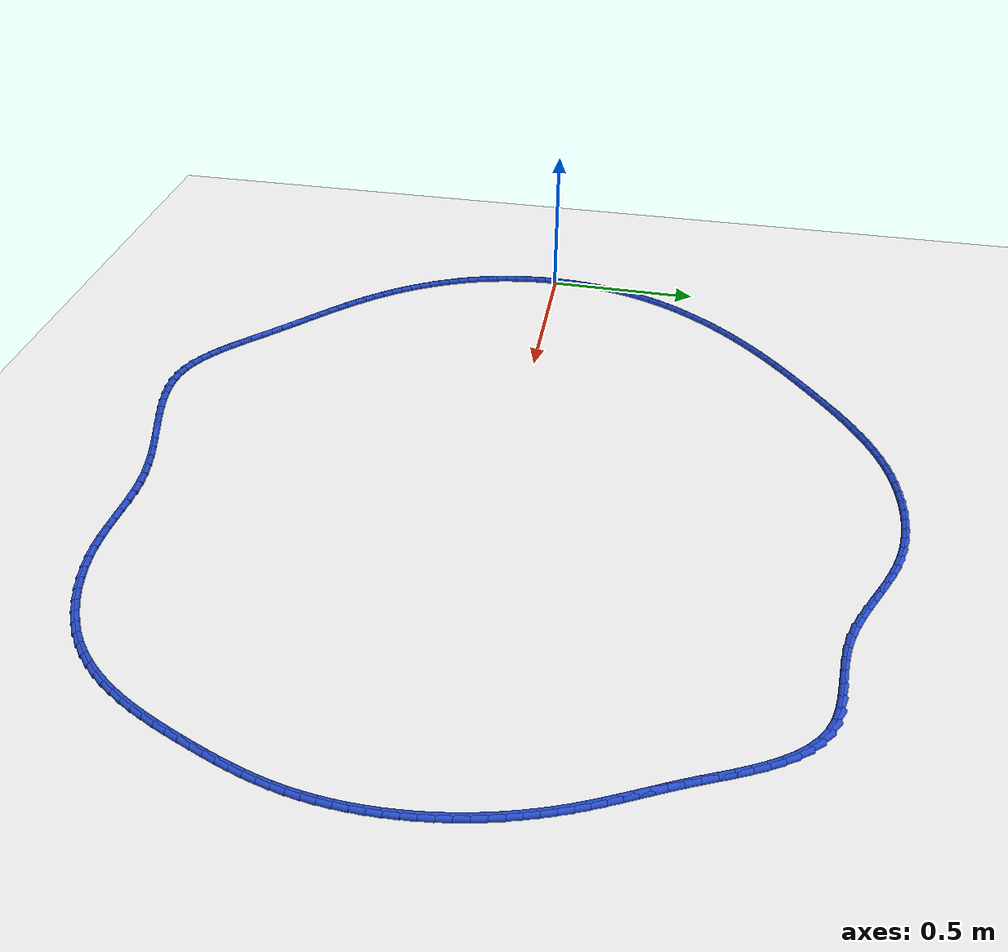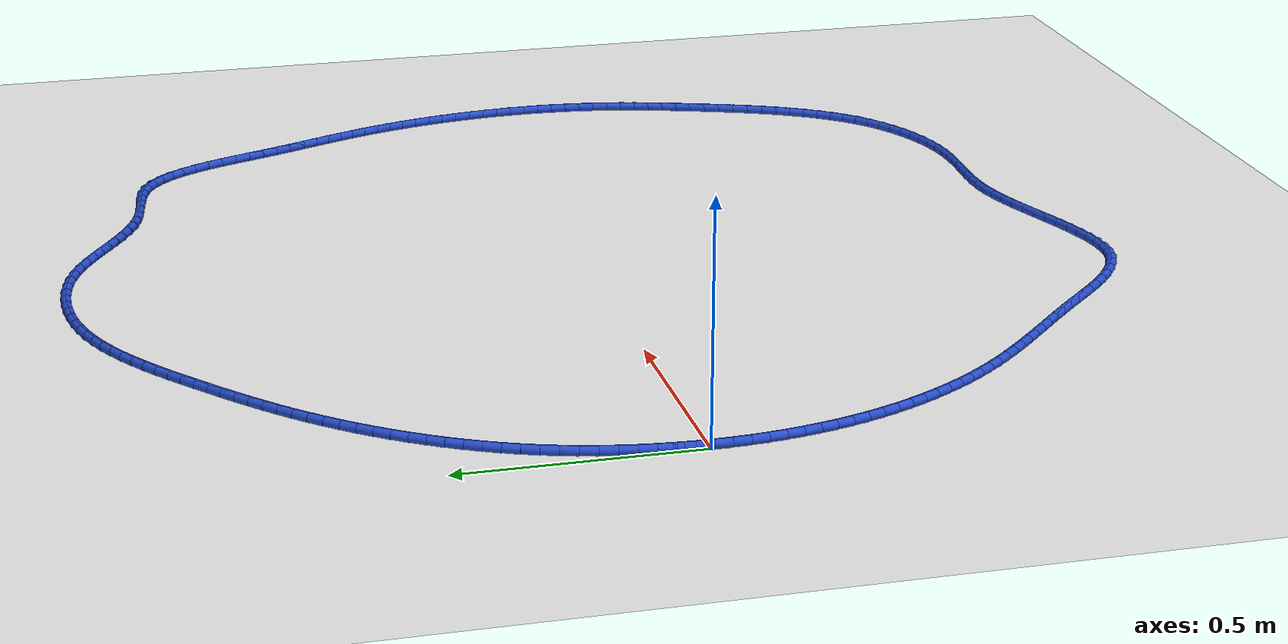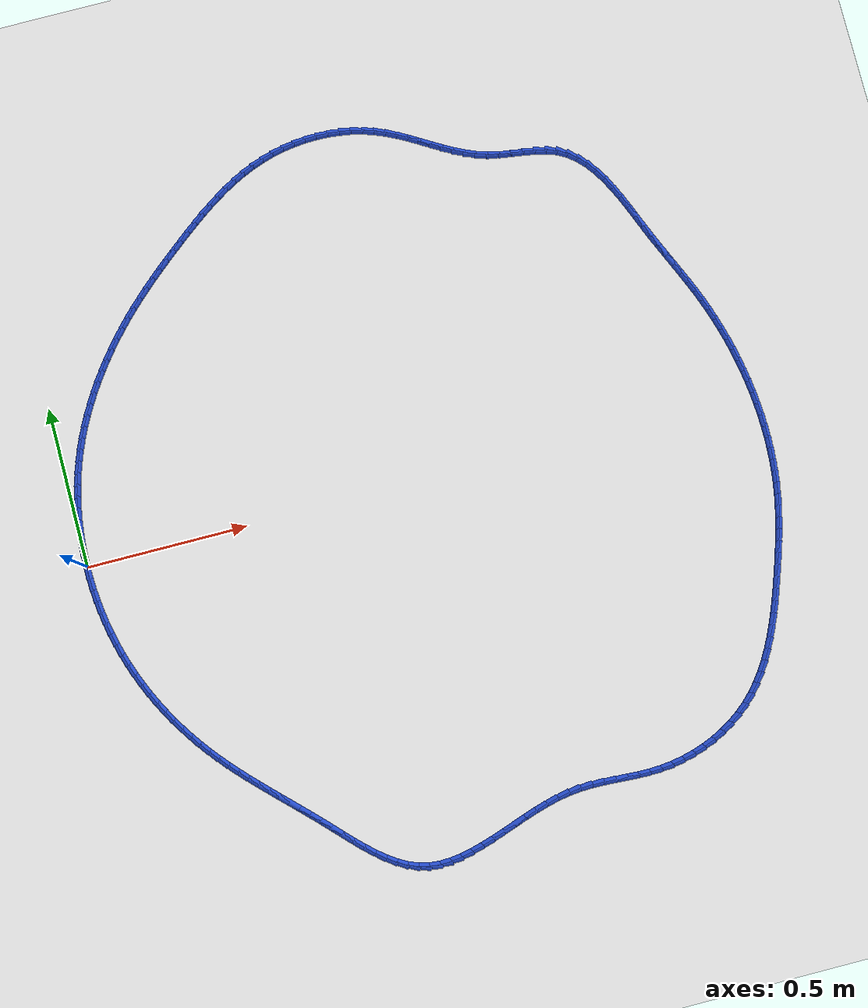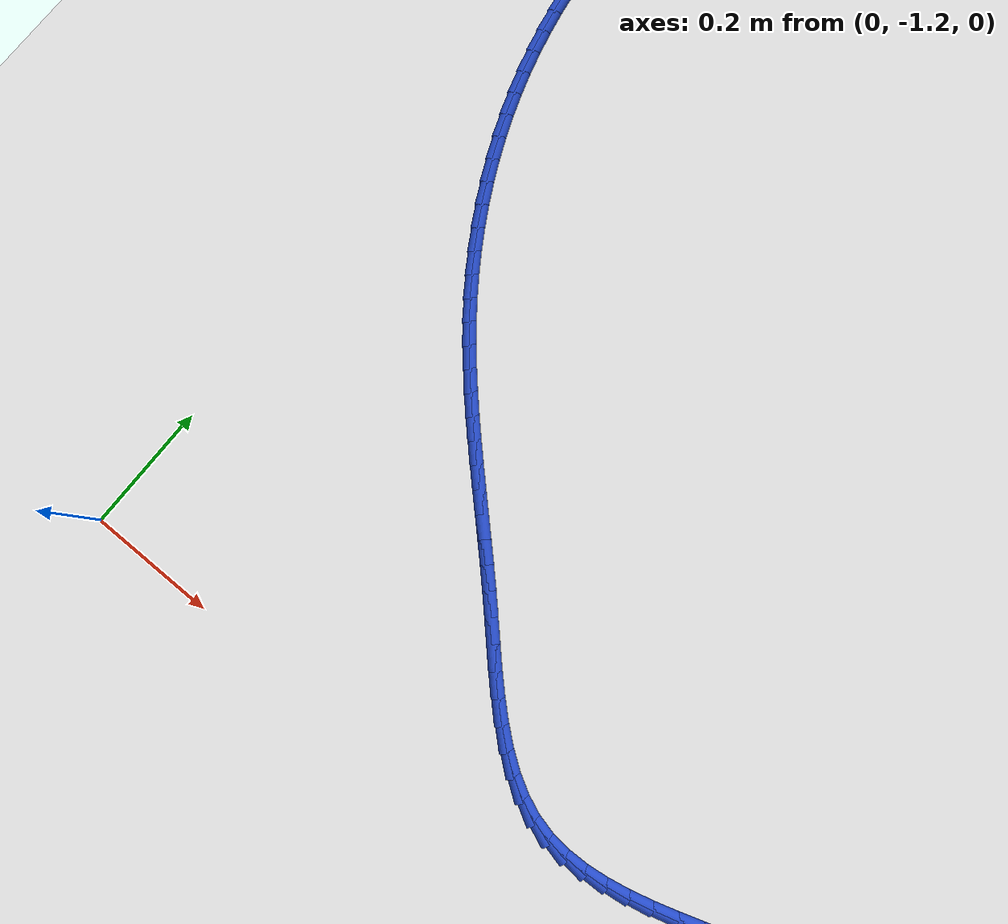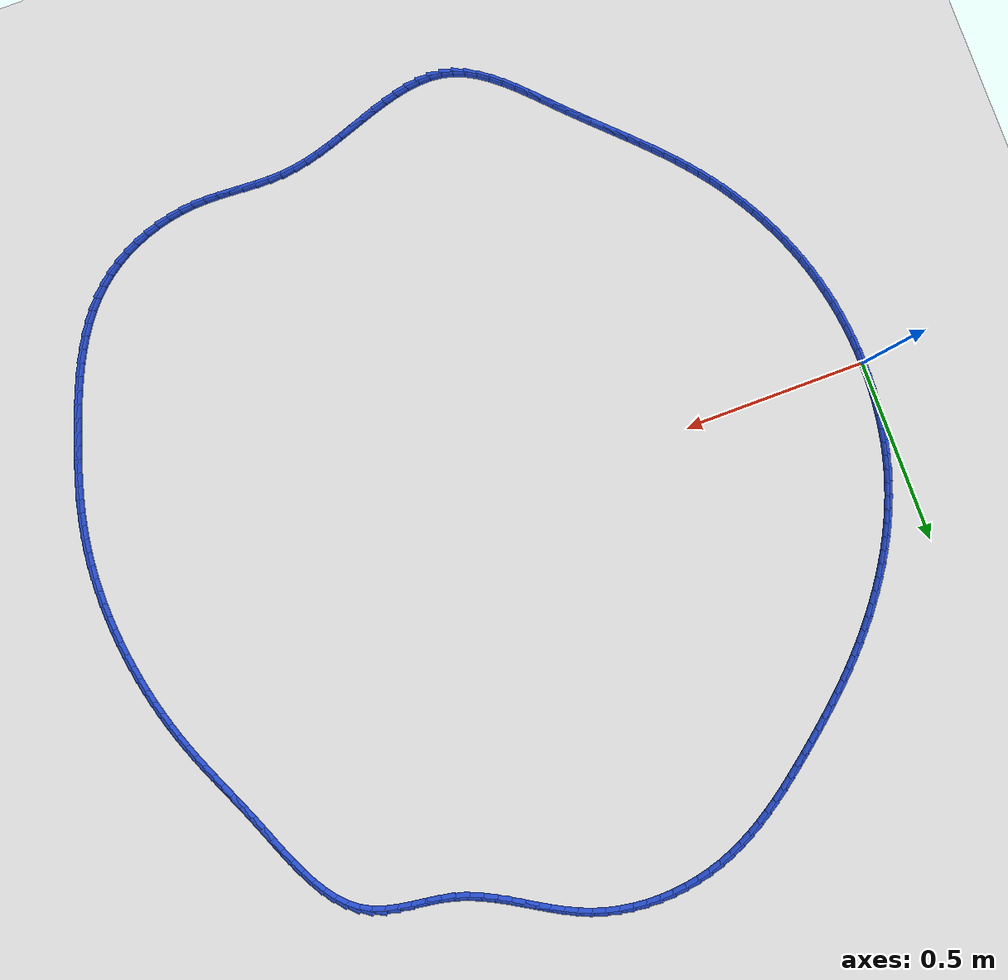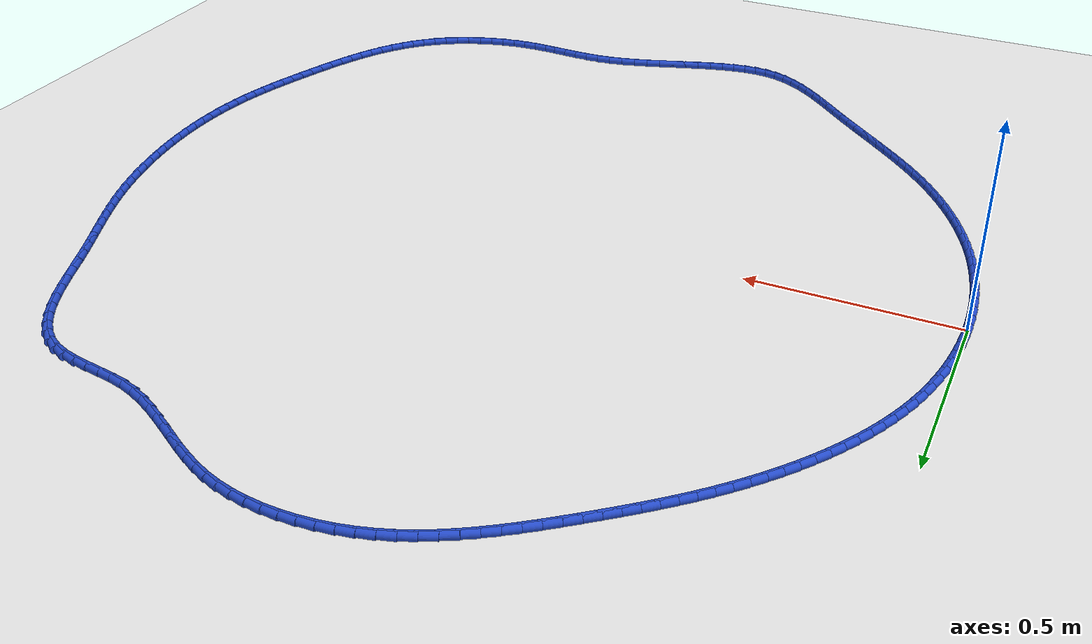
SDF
<sdf version="1.6">
 <world name="default">
  <light name="sun" type="directional">
   <pose>0 0 10 0 -0 0</pose>
   <diffuse>0.8 0.8 0.8 1</diffuse>
   <specular>0.2 0.2 0.2 1</specular>
   <attenuation>
    <range>1000</range>
    <constant>0.9</constant>
    <linear>0.01</linear>
    <quadratic>0.001</quadratic>
   </attenuation>
   <direction>-0.5 0.1 -0.9</direction>
  </light>
  <model name="ground_plane">
   <static>1</static>
   <link name="link">
    <collision name="collision">
     <geometry><plane><normal>0 0 1</normal><size>100 100</size></plane></geometry>
     <surface><friction><ode><mu>100</mu><mu2>50</mu2></ode></friction></surface>
    </collision>
    <visual name="visual">
     <cast_shadows>0</cast_shadows>
     <geometry><plane><normal>0 0 1</normal><size>100 100</size></plane></geometry>
     <material>
      <script><uri>file://media/materials/scripts/gazebo.material</uri><name>Gazebo/WhiteGlow</name></script>
     </material>
    </visual>
   </link>
  </model>
  <gravity>0 0 -9.8</gravity>
  <magnetic_field>6e-06 2.3e-05 -4.2e-05</magnetic_field>
  <atmosphere type="adiabatic"/>
  <physics name="default_physics" default="0" type="ode">
   <max_step_size>0.001</max_step_size>
   <real_time_factor>1</real_time_factor>
   <real_time_update_rate>1000</real_time_update_rate>
  </physics>
  <scene><ambient>0.4 0.4 0.4 1</ambient><background>0.7 0.7 0.7 1</background><shadows>1</shadows></scene>
  <spherical_coordinates>
   <surface_model>EARTH_WGS84</surface_model>
   <latitude_deg>0</latitude_deg>
   <longitude_deg>0</longitude_deg>
   <elevation>0</elevation>
   <heading_deg>0</heading_deg>
  </spherical_coordinates>
  <model name="line">
   <link name="link_0">
    <pose>-2.7755575615628914e-17 6.938893903907228e-17 0.01 0 1.57 1.554966024899362</pose>
    <collision name="collision">
     <geometry><cylinder><radius>0.01</radius><length>0.08</length></cylinder></geometry>
    </collision>
    <visual name="visual">
     <material>
      <script><name>Gazebo/Blue</name><uri>file://media/materials/scripts/gazebo.material</uri></script>
     </material>
     <geometry><cylinder><radius>0.01</radius><length>0.08</length></cylinder></geometry>
    </visual>
   </link>
   <link name="link_1">
    <pose>0.0005712090992517886 0.03608025845099343 0.01 0 1.57 1.519783732723637</pose>
    <collision name="collision">
     <geometry><cylinder><radius>0.01</radius><length>0.08</length></cylinder></geometry>
    </collision>
    <visual name="visual">
     <material>
      <script><name>Gazebo/Blue</name><uri>file://media/materials/scripts/gazebo.material</uri></script>
     </material>
     <geometry><cylinder><radius>0.01</radius><length>0.08</length></cylinder></geometry>
    </visual>
   </link>
   <link name="link_2">
    <pose>0.0024117978563944482 0.07213002096325959 0.01 0 1.57 1.484111538467074</pose>
    <collision name="collision">
     <geometry><cylinder><radius>0.01</radius><length>0.08</length></cylinder></geometry>
    </collision>
    <visual name="visual">
     <material>
      <script><name>Gazebo/Blue</name><uri>file://media/materials/scripts/gazebo.material</uri></script>
     </material>
     <geometry><cylinder><radius>0.01</radius><length>0.08</length></cylinder></geometry>
    </visual>
   </link>
   <link name="link_3">
    <pose>0.005537018427434216 0.10809237154542371 0.01 0 1.57 1.4478751126077472</pose>
    <collision name="collision">
     <geometry><cylinder><radius>0.01</radius><length>0.08</length></cylinder></geometry>
    </collision>
    <visual name="visual">
     <material>
      <script><name>Gazebo/Blue</name><uri>file://media/materials/scripts/gazebo.material</uri></script>
     </material>
     <geometry><cylinder><radius>0.01</radius><length>0.08</length></cylinder></geometry>
    </visual>
   </link>
   <link name="link_4">
    <pose>0.009962122968377368 0.14391039420611088 0.01 0 1.57 1.4110036401615895</pose>
    <collision name="collision">
     <geometry><cylinder><radius>0.01</radius><length>0.08</length></cylinder></geometry>
    </collision>
    <visual name="visual">
     <material>
      <script><name>Gazebo/Blue</name><uri>file://media/materials/scripts/gazebo.material</uri></script>
     </material>
     <geometry><cylinder><radius>0.01</radius><length>0.08</length></cylinder></geometry>
    </visual>
   </link>
   <link name="link_5">
    <pose>0.01570236363523017 0.17952717295394618 0.01 0 1.57 1.3734305395378306</pose>
    <collision name="collision">
     <geometry><cylinder><radius>0.01</radius><length>0.08</length></cylinder></geometry>
    </collision>
    <visual name="visual">
     <material>
      <script><name>Gazebo/Blue</name><uri>file://media/materials/scripts/gazebo.material</uri></script>
     </material>
     <geometry><cylinder><radius>0.01</radius><length>0.08</length></cylinder></geometry>
    </visual>
   </link>
   <link name="link_6">
    <pose>0.02277299258399889 0.21488579179755463 0.01 0 1.57 1.3350943428944009</pose>
    <collision name="collision">
     <geometry><cylinder><radius>0.01</radius><length>0.08</length></cylinder></geometry>
    </collision>
    <visual name="visual">
     <material>
      <script><name>Gazebo/Blue</name><uri>file://media/materials/scripts/gazebo.material</uri></script>
     </material>
     <geometry><cylinder><radius>0.01</radius><length>0.08</length></cylinder></geometry>
    </visual>
   </link>
   <link name="link_7">
    <pose>0.03118926197068978 0.24992933474556134 0.01 0 1.57 1.2959397444328438</pose>
    <collision name="collision">
     <geometry><cylinder><radius>0.01</radius><length>0.08</length></cylinder></geometry>
    </collision>
    <visual name="visual">
     <material>
      <script><name>Gazebo/Blue</name><uri>file://media/materials/scripts/gazebo.material</uri></script>
     </material>
     <geometry><cylinder><radius>0.01</radius><length>0.08</length></cylinder></geometry>
    </visual>
   </link>
   <link name="link_8">
    <pose>0.04096642395130913 0.2846008858065915 0.01 0 1.57 1.2559188156809742</pose>
    <collision name="collision">
     <geometry><cylinder><radius>0.01</radius><length>0.08</length></cylinder></geometry>
    </collision>
    <visual name="visual">
     <material>
      <script><name>Gazebo/Blue</name><uri>file://media/materials/scripts/gazebo.material</uri></script>
     </material>
     <geometry><cylinder><radius>0.01</radius><length>0.08</length></cylinder></geometry>
    </visual>
   </link>
   <link name="link_9">
    <pose>0.052119730681863215 0.31884352898927004 0.01 0 1.57 1.2152198327130048</pose>
    <collision name="collision">
     <geometry><cylinder><radius>0.01</radius><length>0.08</length></cylinder></geometry>
    </collision>
    <visual name="visual">
     <material>
      <script><name>Gazebo/Blue</name><uri>file://media/materials/scripts/gazebo.material</uri></script>
     </material>
     <geometry><cylinder><radius>0.01</radius><length>0.08</length></cylinder></geometry>
    </visual>
   </link>
   <link name="link_10">
    <pose>0.06465711452558207 0.3526041667671321 0.01 0 1.57 1.1753621489340544</pose>
    <collision name="collision">
     <geometry><cylinder><radius>0.01</radius><length>0.08</length></cylinder></geometry>
    </collision>
    <visual name="visual">
     <material>
      <script><name>Gazebo/Blue</name><uri>file://media/materials/scripts/gazebo.material</uri></script>
     </material>
     <geometry><cylinder><radius>0.01</radius><length>0.08</length></cylinder></geometry>
    </visual>
   </link>
   <link name="link_11">
    <pose>0.07853695887582197 0.38585554947697476 0.01 0 1.57 1.1369782166927267</pose>
    <collision name="collision">
     <geometry><cylinder><radius>0.01</radius><length>0.08</length></cylinder></geometry>
    </collision>
    <visual name="visual">
     <material>
      <script><name>Gazebo/Blue</name><uri>file://media/materials/scripts/gazebo.material</uri></script>
     </material>
     <geometry><cylinder><radius>0.01</radius><length>0.08</length></cylinder></geometry>
    </visual>
   </link>
   <link name="link_12">
    <pose>0.09369710207800608 0.41858114504651694 0.01 0 1.57 1.1000509516635464</pose>
    <collision name="collision">
     <geometry><cylinder><radius>0.01</radius><length>0.08</length></cylinder></geometry>
    </collision>
    <visual name="visual">
     <material>
      <script><name>Gazebo/Blue</name><uri>file://media/materials/scripts/gazebo.material</uri></script>
     </material>
     <geometry><cylinder><radius>0.01</radius><length>0.08</length></cylinder></geometry>
    </visual>
   </link>
   <link name="link_13">
    <pose>0.11007531630858591 0.4507644559213801 0.01 0 1.57 1.0645469594919728</pose>
    <collision name="collision">
     <geometry><cylinder><radius>0.01</radius><length>0.08</length></cylinder></geometry>
    </collision>
    <visual name="visual">
     <material>
      <script><name>Gazebo/Blue</name><uri>file://media/materials/scripts/gazebo.material</uri></script>
     </material>
     <geometry><cylinder><radius>0.01</radius><length>0.08</length></cylinder></geometry>
    </visual>
   </link>
   <link name="link_14">
    <pose>0.12760937374401324 0.48238898454718593 0.01 0 1.57 1.0304212655724954</pose>
    <collision name="collision">
     <geometry><cylinder><radius>0.01</radius><length>0.08</length></cylinder></geometry>
    </collision>
    <visual name="visual">
     <material>
      <script><name>Gazebo/Blue</name><uri>file://media/materials/scripts/gazebo.material</uri></script>
     </material>
     <geometry><cylinder><radius>0.01</radius><length>0.08</length></cylinder></geometry>
    </visual>
   </link>
   <link name="link_15">
    <pose>0.14623704656073966 0.513438233369556 0.01 0 1.57 0.9976197381627456</pose>
    <collision name="collision">
     <geometry><cylinder><radius>0.01</radius><length>0.08</length></cylinder></geometry>
    </collision>
    <visual name="visual">
     <material>
      <script><name>Gazebo/Blue</name><uri>file://media/materials/scripts/gazebo.material</uri></script>
     </material>
     <geometry><cylinder><radius>0.01</radius><length>0.08</length></cylinder></geometry>
    </visual>
   </link>
   <link name="link_16">
    <pose>0.1658961069352168 0.5438957048341119 0.01 0 1.57 0.9660812131487029</pose>
    <collision name="collision">
     <geometry><cylinder><radius>0.01</radius><length>0.08</length></cylinder></geometry>
    </collision>
    <visual name="visual">
     <material>
      <script><name>Gazebo/Blue</name><uri>file://media/materials/scripts/gazebo.material</uri></script>
     </material>
     <geometry><cylinder><radius>0.01</radius><length>0.08</length></cylinder></geometry>
    </visual>
   </link>
   <link name="link_17">
    <pose>0.18652432704389635 0.5737449013864753 0.01 0 1.57 0.9357393013796473</pose>
    <collision name="collision">
     <geometry><cylinder><radius>0.01</radius><length>0.08</length></cylinder></geometry>
    </collision>
    <visual name="visual">
     <material>
      <script><name>Gazebo/Blue</name><uri>file://media/materials/scripts/gazebo.material</uri></script>
     </material>
     <geometry><cylinder><radius>0.01</radius><length>0.08</length></cylinder></geometry>
    </visual>
   </link>
   <link name="link_18">
    <pose>0.20805947906322983 0.6029693254722677 0.01 0 1.57 0.9065238802734443</pose>
    <collision name="collision">
     <geometry><cylinder><radius>0.01</radius><length>0.08</length></cylinder></geometry>
    </collision>
    <visual name="visual">
     <material>
      <script><name>Gazebo/Blue</name><uri>file://media/materials/scripts/gazebo.material</uri></script>
     </material>
     <geometry><cylinder><radius>0.01</radius><length>0.08</length></cylinder></geometry>
    </visual>
   </link>
   <link name="link_19">
    <pose>0.23043933516966894 0.6315524795371105 0.01 0 1.57 0.8783622851384897</pose>
    <collision name="collision">
     <geometry><cylinder><radius>0.01</radius><length>0.08</length></cylinder></geometry>
    </collision>
    <visual name="visual">
     <material>
      <script><name>Gazebo/Blue</name><uri>file://media/materials/scripts/gazebo.material</uri></script>
     </material>
     <geometry><cylinder><radius>0.01</radius><length>0.08</length></cylinder></geometry>
    </visual>
   </link>
   <link name="link_20">
    <pose>0.2536016675396654 0.6594778660266256 0.01 0 1.57 0.8511802236176552</pose>
    <collision name="collision">
     <geometry><cylinder><radius>0.01</radius><length>0.08</length></cylinder></geometry>
    </collision>
    <visual name="visual">
     <material>
      <script><name>Gazebo/Blue</name><uri>file://media/materials/scripts/gazebo.material</uri></script>
     </material>
     <geometry><cylinder><radius>0.01</radius><length>0.08</length></cylinder></geometry>
    </visual>
   </link>
   <link name="link_21">
    <pose>0.2774842483496707 0.6867289873864345 0.01 0 1.57 0.8249024401533396</pose>
    <collision name="collision">
     <geometry><cylinder><radius>0.01</radius><length>0.08</length></cylinder></geometry>
    </collision>
    <visual name="visual">
     <material>
      <script><name>Gazebo/Blue</name><uri>file://media/materials/scripts/gazebo.material</uri></script>
     </material>
     <geometry><cylinder><radius>0.01</radius><length>0.08</length></cylinder></geometry>
    </visual>
   </link>
   <link name="link_22">
    <pose>0.30202484977613675 0.7132893460621589 0.01 0 1.57 0.7994531576061562</pose>
    <collision name="collision">
     <geometry><cylinder><radius>0.01</radius><length>0.08</length></cylinder></geometry>
    </collision>
    <visual name="visual">
     <material>
      <script><name>Gazebo/Blue</name><uri>file://media/materials/scripts/gazebo.material</uri></script>
     </material>
     <geometry><cylinder><radius>0.01</radius><length>0.08</length></cylinder></geometry>
    </visual>
   </link>
   <link name="link_23">
    <pose>0.3271612439955148 0.73914244449942 0.01 0 1.57 0.7750389813281787</pose>
    <collision name="collision">
     <geometry><cylinder><radius>0.01</radius><length>0.08</length></cylinder></geometry>
    </collision>
    <visual name="visual">
     <material>
      <script><name>Gazebo/Blue</name><uri>file://media/materials/scripts/gazebo.material</uri></script>
     </material>
     <geometry><cylinder><radius>0.01</radius><length>0.08</length></cylinder></geometry>
    </visual>
   </link>
   <link name="link_24">
    <pose>0.35283468434584553 0.7642894081986968 0.01 0 1.57 0.7528235333998068</pose>
    <collision name="collision">
     <geometry><cylinder><radius>0.01</radius><length>0.08</length></cylinder></geometry>
    </collision>
    <visual name="visual">
     <material>
      <script><name>Gazebo/Blue</name><uri>file://media/materials/scripts/gazebo.material</uri></script>
     </material>
     <geometry><cylinder><radius>0.01</radius><length>0.08</length></cylinder></geometry>
    </visual>
   </link>
   <link name="link_25">
    <pose>0.3790007743834465 0.7888040092979378 0.01 0 1.57 0.7331987667338619</pose>
    <collision name="collision">
     <geometry><cylinder><radius>0.01</radius><length>0.08</length></cylinder></geometry>
    </collision>
    <visual name="visual">
     <material>
      <script><name>Gazebo/Blue</name><uri>file://media/materials/scripts/gazebo.material</uri></script>
     </material>
     <geometry><cylinder><radius>0.01</radius><length>0.08</length></cylinder></geometry>
    </visual>
   </link>
   <link name="link_26">
    <pose>0.4056188148437434 0.8127787365584292 0.01 0 1.57 0.7162407769315573</pose>
    <collision name="collision">
     <geometry><cylinder><radius>0.01</radius><length>0.08</length></cylinder></geometry>
    </collision>
    <visual name="visual">
     <material>
      <script><name>Gazebo/Blue</name><uri>file://media/materials/scripts/gazebo.material</uri></script>
     </material>
     <geometry><cylinder><radius>0.01</radius><length>0.08</length></cylinder></geometry>
    </visual>
   </link>
   <link name="link_27">
    <pose>0.432648106465787 0.8363060787598108 0.01 0 1.57 0.7020008636373285</pose>
    <collision name="collision">
     <geometry><cylinder><radius>0.01</radius><length>0.08</length></cylinder></geometry>
    </collision>
    <visual name="visual">
     <material>
      <script><name>Gazebo/Blue</name><uri>file://media/materials/scripts/gazebo.material</uri></script>
     </material>
     <geometry><cylinder><radius>0.01</radius><length>0.08</length></cylinder></geometry>
    </visual>
   </link>
   <link name="link_28">
    <pose>0.4600479499886284 0.8594785246817216 0.01 0 1.57 0.6905085745159842</pose>
    <collision name="collision">
     <geometry><cylinder><radius>0.01</radius><length>0.08</length></cylinder></geometry>
    </collision>
    <visual name="visual">
     <material>
      <script><name>Gazebo/Blue</name><uri>file://media/materials/scripts/gazebo.material</uri></script>
     </material>
     <geometry><cylinder><radius>0.01</radius><length>0.08</length></cylinder></geometry>
    </visual>
   </link>
   <link name="link_29">
    <pose>0.4877776461513184 0.8823885631038004 0.01 0 1.57 0.6817646961395754</pose>
    <collision name="collision">
     <geometry><cylinder><radius>0.01</radius><length>0.08</length></cylinder></geometry>
    </collision>
    <visual name="visual">
     <material>
      <script><name>Gazebo/Blue</name><uri>file://media/materials/scripts/gazebo.material</uri></script>
     </material>
     <geometry><cylinder><radius>0.01</radius><length>0.08</length></cylinder></geometry>
    </visual>
   </link>
   <link name="link_30">
    <pose>0.5157966294236228 0.9051283283145938 0.01 0 1.57 0.6735046634133595</pose>
    <collision name="collision">
     <geometry><cylinder><radius>0.01</radius><length>0.08</length></cylinder></geometry>
    </collision>
    <visual name="visual">
     <material>
      <script><name>Gazebo/Blue</name><uri>file://media/materials/scripts/gazebo.material</uri></script>
     </material>
     <geometry><cylinder><radius>0.01</radius><length>0.08</length></cylinder></geometry>
    </visual>
   </link>
   <link name="link_31">
    <pose>0.5440946984006064 0.92770946589841 0.01 0 1.57 0.6606003718626808</pose>
    <collision name="collision">
     <geometry><cylinder><radius>0.01</radius><length>0.08</length></cylinder></geometry>
    </collision>
    <visual name="visual">
     <material>
      <script><name>Gazebo/Blue</name><uri>file://media/materials/scripts/gazebo.material</uri></script>
     </material>
     <geometry><cylinder><radius>0.01</radius><length>0.08</length></cylinder></geometry>
    </visual>
   </link>
   <link name="link_32">
    <pose>0.5727304144705806 0.9499613462027869 0.01 0 1.57 0.6423070653801735</pose>
    <collision name="collision">
     <geometry><cylinder><radius>0.01</radius><length>0.08</length></cylinder></geometry>
    </collision>
    <visual name="visual">
     <material>
      <script><name>Gazebo/Blue</name><uri>file://media/materials/scripts/gazebo.material</uri></script>
     </material>
     <geometry><cylinder><radius>0.01</radius><length>0.08</length></cylinder></geometry>
    </visual>
   </link>
   <link name="link_33">
    <pose>0.6017718026709176 0.9716882534961189 0.01 0 1.57 0.6185427021361295</pose>
    <collision name="collision">
     <geometry><cylinder><radius>0.01</radius><length>0.08</length></cylinder></geometry>
    </collision>
    <visual name="visual">
     <material>
      <script><name>Gazebo/Blue</name><uri>file://media/materials/scripts/gazebo.material</uri></script>
     </material>
     <geometry><cylinder><radius>0.01</radius><length>0.08</length></cylinder></geometry>
    </visual>
   </link>
   <link name="link_34">
    <pose>0.631286888038991 0.9926944720468023 0.01 0 1.57 0.5891980538573569</pose>
    <collision name="collision">
     <geometry><cylinder><radius>0.01</radius><length>0.08</length></cylinder></geometry>
    </collision>
    <visual name="visual">
     <material>
      <script><name>Gazebo/Blue</name><uri>file://media/materials/scripts/gazebo.material</uri></script>
     </material>
     <geometry><cylinder><radius>0.01</radius><length>0.08</length></cylinder></geometry>
    </visual>
   </link>
   <link name="link_35">
    <pose>0.6613436956121731 1.0127842861232328 0.01 0 1.57 0.5541574567162315</pose>
    <collision name="collision">
     <geometry><cylinder><radius>0.01</radius><length>0.08</length></cylinder></geometry>
    </collision>
    <visual name="visual">
     <material>
      <script><name>Gazebo/Blue</name><uri>file://media/materials/scripts/gazebo.material</uri></script>
     </material>
     <geometry><cylinder><radius>0.01</radius><length>0.08</length></cylinder></geometry>
    </visual>
   </link>
   <link name="link_36">
    <pose>0.6920102504278363 1.0317619799938054 0.01 0 1.57 0.5133262465839459</pose>
    <collision name="collision">
     <geometry><cylinder><radius>0.01</radius><length>0.08</length></cylinder></geometry>
    </collision>
    <visual name="visual">
     <material>
      <script><name>Gazebo/Blue</name><uri>file://media/materials/scripts/gazebo.material</uri></script>
     </material>
     <geometry><cylinder><radius>0.01</radius><length>0.08</length></cylinder></geometry>
    </visual>
   </link>
   <link name="link_37">
    <pose>0.7233545775233543 1.0494318379269165 0.01 0 1.57 0.46666562736941286</pose>
    <collision name="collision">
     <geometry><cylinder><radius>0.01</radius><length>0.08</length></cylinder></geometry>
    </collision>
    <visual name="visual">
     <material>
      <script><name>Gazebo/Blue</name><uri>file://media/materials/scripts/gazebo.material</uri></script>
     </material>
     <geometry><cylinder><radius>0.01</radius><length>0.08</length></cylinder></geometry>
    </visual>
   </link>
   <link name="link_38">
    <pose>0.7554447019360988 1.0655981441909608 0.01 0 1.57 0.4142344563140027</pose>
    <collision name="collision">
     <geometry><cylinder><radius>0.01</radius><length>0.08</length></cylinder></geometry>
    </collision>
    <visual name="visual">
     <material>
      <script><name>Gazebo/Blue</name><uri>file://media/materials/scripts/gazebo.material</uri></script>
     </material>
     <geometry><cylinder><radius>0.01</radius><length>0.08</length></cylinder></geometry>
    </visual>
   </link>
   <link name="link_39">
    <pose>0.7883486487034435 1.0800651830543349 0.01 0 1.57 0.3562351879163544</pose>
    <collision name="collision">
     <geometry><cylinder><radius>0.01</radius><length>0.08</length></cylinder></geometry>
    </collision>
    <visual name="visual">
     <material>
      <script><name>Gazebo/Blue</name><uri>file://media/materials/scripts/gazebo.material</uri></script>
     </material>
     <geometry><cylinder><radius>0.01</radius><length>0.08</length></cylinder></geometry>
    </visual>
   </link>
   <link name="link_40">
    <pose>0.8221344428627603 1.0926372387854333 0.01 0 1.57 0.29329104934760364</pose>
    <collision name="collision">
     <geometry><cylinder><radius>0.01</radius><length>0.08</length></cylinder></geometry>
    </collision>
    <visual name="visual">
     <material>
      <script><name>Gazebo/Blue</name><uri>file://media/materials/scripts/gazebo.material</uri></script>
     </material>
     <geometry><cylinder><radius>0.01</radius><length>0.08</length></cylinder></geometry>
    </visual>
   </link>
   <link name="link_41">
    <pose>0.8568594252054567 1.1031241987613323 0.01 0 1.57 0.22909867496569786</pose>
    <collision name="collision">
     <geometry><cylinder><radius>0.01</radius><length>0.08</length></cylinder></geometry>
    </collision>
    <visual name="visual">
     <material>
      <script><name>Gazebo/Blue</name><uri>file://media/materials/scripts/gazebo.material</uri></script>
     </material>
     <geometry><cylinder><radius>0.01</radius><length>0.08</length></cylinder></geometry>
    </visual>
   </link>
   <link name="link_42">
    <pose>0.892424857597681 1.1114178023853174 0.01 0 1.57 0.1657538611003626</pose>
    <collision name="collision">
     <geometry><cylinder><radius>0.01</radius><length>0.08</length></cylinder></geometry>
    </collision>
    <visual name="visual">
     <material>
      <script><name>Gazebo/Blue</name><uri>file://media/materials/scripts/gazebo.material</uri></script>
     </material>
     <geometry><cylinder><radius>0.01</radius><length>0.08</length></cylinder></geometry>
    </visual>
   </link>
   <link name="link_43">
    <pose>0.9286137609273181 1.1174717978401187 0.01 0 1.57 0.10265564131967057</pose>
    <collision name="collision">
     <geometry><cylinder><radius>0.01</radius><length>0.08</length></cylinder></geometry>
    </collision>
    <visual name="visual">
     <material>
      <script><name>Gazebo/Blue</name><uri>file://media/materials/scripts/gazebo.material</uri></script>
     </material>
     <geometry><cylinder><radius>0.01</radius><length>0.08</length></cylinder></geometry>
    </visual>
   </link>
   <link name="link_44">
    <pose>0.9652062227575235 1.1212414716235972 0.01 0 1.57 0.03915320200424404</pose>
    <collision name="collision">
     <geometry><cylinder><radius>0.01</radius><length>0.08</length></cylinder></geometry>
    </collision>
    <visual name="visual">
     <material>
      <script><name>Gazebo/Blue</name><uri>file://media/materials/scripts/gazebo.material</uri></script>
     </material>
     <geometry><cylinder><radius>0.01</radius><length>0.08</length></cylinder></geometry>
    </visual>
   </link>
   <link name="link_45">
    <pose>1.0019823306514533 1.1226821102336157 0.01 0 1.57 -0.025392311762200307</pose>
    <collision name="collision">
     <geometry><cylinder><radius>0.01</radius><length>0.08</length></cylinder></geometry>
    </collision>
    <visual name="visual">
     <material>
      <script><name>Gazebo/Blue</name><uri>file://media/materials/scripts/gazebo.material</uri></script>
     </material>
     <geometry><cylinder><radius>0.01</radius><length>0.08</length></cylinder></geometry>
    </visual>
   </link>
   <link name="link_46">
    <pose>1.0387221721722624 1.1217490001680355 0.01 0 1.57 -0.09160789442999658</pose>
    <collision name="collision">
     <geometry><cylinder><radius>0.01</radius><length>0.08</length></cylinder></geometry>
    </collision>
    <visual name="visual">
     <material>
      <script><name>Gazebo/Blue</name><uri>file://media/materials/scripts/gazebo.material</uri></script>
     </material>
     <geometry><cylinder><radius>0.01</radius><length>0.08</length></cylinder></geometry>
    </visual>
   </link>
   <link name="link_47">
    <pose>1.075205834883107 1.118397427924719 0.01 0 1.57 -0.16010462466605127</pose>
    <collision name="collision">
     <geometry><cylinder><radius>0.01</radius><length>0.08</length></cylinder></geometry>
    </collision>
    <visual name="visual">
     <material>
      <script><name>Gazebo/Blue</name><uri>file://media/materials/scripts/gazebo.material</uri></script>
     </material>
     <geometry><cylinder><radius>0.01</radius><length>0.08</length></cylinder></geometry>
    </visual>
   </link>
   <link name="link_48">
    <pose>1.1112134063471428 1.112582680001528 0.01 0 1.57 -0.23146718941003985</pose>
    <collision name="collision">
     <geometry><cylinder><radius>0.01</radius><length>0.08</length></cylinder></geometry>
    </collision>
    <visual name="visual">
     <material>
      <script><name>Gazebo/Blue</name><uri>file://media/materials/scripts/gazebo.material</uri></script>
     </material>
     <geometry><cylinder><radius>0.01</radius><length>0.08</length></cylinder></geometry>
    </visual>
   </link>
   <link name="link_49">
    <pose>1.1465249741275252 1.1042600428963245 0.01 0 1.57 -0.3062345435214308</pose>
    <collision name="collision">
     <geometry><cylinder><radius>0.01</radius><length>0.08</length></cylinder></geometry>
    </collision>
    <visual name="visual">
     <material>
      <script><name>Gazebo/Blue</name><uri>file://media/materials/scripts/gazebo.material</uri></script>
     </material>
     <geometry><cylinder><radius>0.01</radius><length>0.08</length></cylinder></geometry>
    </visual>
   </link>
   <link name="link_50">
    <pose>1.1809206257874103 1.0933848031069704 0.01 0 1.57 -0.3833064386205607</pose>
    <collision name="collision">
     <geometry><cylinder><radius>0.01</radius><length>0.08</length></cylinder></geometry>
    </collision>
    <visual name="visual">
     <material>
      <script><name>Gazebo/Blue</name><uri>file://media/materials/scripts/gazebo.material</uri></script>
     </material>
     <geometry><cylinder><radius>0.01</radius><length>0.08</length></cylinder></geometry>
    </visual>
   </link>
   <link name="link_51">
    <pose>1.214215871334835 1.0799584380103464 0.01 0 1.57 -0.4492917388914051</pose>
    <collision name="collision">
     <geometry><cylinder><radius>0.01</radius><length>0.08</length></cylinder></geometry>
    </collision>
    <visual name="visual">
     <material>
      <script><name>Gazebo/Blue</name><uri>file://media/materials/scripts/gazebo.material</uri></script>
     </material>
     <geometry><cylinder><radius>0.01</radius><length>0.08</length></cylinder></geometry>
    </visual>
   </link>
   <link name="link_52">
    <pose>1.2465292156130734 1.0643775303416616 0.01 0 1.57 -0.496903094330329</pose>
    <collision name="collision">
     <geometry><cylinder><radius>0.01</radius><length>0.08</length></cylinder></geometry>
    </collision>
    <visual name="visual">
     <material>
      <script><name>Gazebo/Blue</name><uri>file://media/materials/scripts/gazebo.material</uri></script>
     </material>
     <geometry><cylinder><radius>0.01</radius><length>0.08</length></cylinder></geometry>
    </visual>
   </link>
   <link name="link_53">
    <pose>1.2781329503566745 1.0472392009896412 0.01 0 1.57 -0.5260598898519439</pose>
    <collision name="collision">
     <geometry><cylinder><radius>0.01</radius><length>0.08</length></cylinder></geometry>
    </collision>
    <visual name="visual">
     <material>
      <script><name>Gazebo/Blue</name><uri>file://media/materials/scripts/gazebo.material</uri></script>
     </material>
     <geometry><cylinder><radius>0.01</radius><length>0.08</length></cylinder></geometry>
    </visual>
   </link>
   <link name="link_54">
    <pose>1.3093005733941907 1.0291421435899613 0.01 0 1.57 -0.5369519230182085</pose>
    <collision name="collision">
     <geometry><cylinder><radius>0.01</radius><length>0.08</length></cylinder></geometry>
    </collision>
    <visual name="visual">
     <material>
      <script><name>Gazebo/Blue</name><uri>file://media/materials/scripts/gazebo.material</uri></script>
     </material>
     <geometry><cylinder><radius>0.01</radius><length>0.08</length></cylinder></geometry>
    </visual>
   </link>
   <link name="link_55">
    <pose>1.3403055825541745 1.0106850517782975 0.01 0 1.57 -0.5296913512938771</pose>
    <collision name="collision">
     <geometry><cylinder><radius>0.01</radius><length>0.08</length></cylinder></geometry>
    </collision>
    <visual name="visual">
     <material>
      <script><name>Gazebo/Blue</name><uri>file://media/materials/scripts/gazebo.material</uri></script>
     </material>
     <geometry><cylinder><radius>0.01</radius><length>0.08</length></cylinder></geometry>
    </visual>
   </link>
   <link name="link_56">
    <pose>1.3714214756651772 0.992466619190326 0.01 0 1.57 -0.5042053317994968</pose>
    <collision name="collision">
     <geometry><cylinder><radius>0.01</radius><length>0.08</length></cylinder></geometry>
    </collision>
    <visual name="visual">
     <material>
      <script><name>Gazebo/Blue</name><uri>file://media/materials/scripts/gazebo.material</uri></script>
     </material>
     <geometry><cylinder><radius>0.01</radius><length>0.08</length></cylinder></geometry>
    </visual>
   </link>
   <link name="link_57">
    <pose>1.4029217505557507 0.9750855394617219 0.01 0 1.57 -0.4603074326827278</pose>
    <collision name="collision">
     <geometry><cylinder><radius>0.01</radius><length>0.08</length></cylinder></geometry>
    </collision>
    <visual name="visual">
     <material>
      <script><name>Gazebo/Blue</name><uri>file://media/materials/scripts/gazebo.material</uri></script>
     </material>
     <geometry><cylinder><radius>0.01</radius><length>0.08</length></cylinder></geometry>
    </visual>
   </link>
   <link name="link_58">
    <pose>1.4350799050544485 0.9591405062281617 0.01 0 1.57 -0.3979539377048277</pose>
    <collision name="collision">
     <geometry><cylinder><radius>0.01</radius><length>0.08</length></cylinder></geometry>
    </collision>
    <visual name="visual">
     <material>
      <script><name>Gazebo/Blue</name><uri>file://media/materials/scripts/gazebo.material</uri></script>
     </material>
     <geometry><cylinder><radius>0.01</radius><length>0.08</length></cylinder></geometry>
    </visual>
   </link>
   <link name="link_59">
    <pose>1.4681694369898206 0.9452302131253209 0.01 0 1.57 -0.31768760493813436</pose>
    <collision name="collision">
     <geometry><cylinder><radius>0.01</radius><length>0.08</length></cylinder></geometry>
    </collision>
    <visual name="visual">
     <material>
      <script><name>Gazebo/Blue</name><uri>file://media/materials/scripts/gazebo.material</uri></script>
     </material>
     <geometry><cylinder><radius>0.01</radius><length>0.08</length></cylinder></geometry>
    </visual>
   </link>
   <link name="link_60">
    <pose>1.5024638441904203 0.9339533537888753 0.01 0 1.57 -0.22659293655149187</pose>
    <collision name="collision">
     <geometry><cylinder><radius>0.01</radius><length>0.08</length></cylinder></geometry>
    </collision>
    <visual name="visual">
     <material>
      <script><name>Gazebo/Blue</name><uri>file://media/materials/scripts/gazebo.material</uri></script>
     </material>
     <geometry><cylinder><radius>0.01</radius><length>0.08</length></cylinder></geometry>
    </visual>
   </link>
   <link name="link_61">
    <pose>1.5381406811920082 0.925727974682842 0.01 0 1.57 -0.16328388565466856</pose>
    <collision name="collision">
     <geometry><cylinder><radius>0.01</radius><length>0.08</length></cylinder></geometry>
    </collision>
    <visual name="visual">
     <material>
      <script><name>Gazebo/Blue</name><uri>file://media/materials/scripts/gazebo.material</uri></script>
     </material>
     <geometry><cylinder><radius>0.01</radius><length>0.08</length></cylinder></geometry>
    </visual>
   </link>
   <link name="link_62">
    <pose>1.5747040624362523 0.9197041331837316 0.01 0 1.57 -0.14129249210785605</pose>
    <collision name="collision">
     <geometry><cylinder><radius>0.01</radius><length>0.08</length></cylinder></geometry>
    </collision>
    <visual name="visual">
     <material>
      <script><name>Gazebo/Blue</name><uri>file://media/materials/scripts/gazebo.material</uri></script>
     </material>
     <geometry><cylinder><radius>0.01</radius><length>0.08</length></cylinder></geometry>
    </visual>
   </link>
   <link name="link_63">
    <pose>1.6113696678114675 0.9144888066386327 0.01 0 1.57 -0.15986665288799948</pose>
    <collision name="collision">
     <geometry><cylinder><radius>0.01</radius><length>0.08</length></cylinder></geometry>
    </collision>
    <visual name="visual">
     <material>
      <script><name>Gazebo/Blue</name><uri>file://media/materials/scripts/gazebo.material</uri></script>
     </material>
     <geometry><cylinder><radius>0.01</radius><length>0.08</length></cylinder></geometry>
    </visual>
   </link>
   <link name="link_64">
    <pose>1.6473520804167625 0.9086869073011572 0.01 0 1.57 -0.22180952474324808</pose>
    <collision name="collision">
     <geometry><cylinder><radius>0.01</radius><length>0.08</length></cylinder></geometry>
    </collision>
    <visual name="visual">
     <material>
      <script><name>Gazebo/Blue</name><uri>file://media/materials/scripts/gazebo.material</uri></script>
     </material>
     <geometry><cylinder><radius>0.01</radius><length>0.08</length></cylinder></geometry>
    </visual>
   </link>
   <link name="link_65">
    <pose>1.6818658833512459 0.900903347424918 0.01 0 1.57 -0.33306332196200183</pose>
    <collision name="collision">
     <geometry><cylinder><radius>0.01</radius><length>0.08</length></cylinder></geometry>
    </collision>
    <visual name="visual">
     <material>
      <script><name>Gazebo/Blue</name><uri>file://media/materials/scripts/gazebo.material</uri></script>
     </material>
     <geometry><cylinder><radius>0.01</radius><length>0.08</length></cylinder></geometry>
    </visual>
   </link>
   <link name="link_66">
    <pose>1.7141256597140246 0.8897430392635272 0.01 0 1.57 -0.49444775255299706</pose>
    <collision name="collision">
     <geometry><cylinder><radius>0.01</radius><length>0.08</length></cylinder></geometry>
    </collision>
    <visual name="visual">
     <material>
      <script><name>Gazebo/Blue</name><uri>file://media/materials/scripts/gazebo.material</uri></script>
     </material>
     <geometry><cylinder><radius>0.01</radius><length>0.08</length></cylinder></geometry>
    </visual>
   </link>
   <link name="link_67">
    <pose>1.7434229790423919 0.8739484172507914 0.01 0 1.57 -0.6610888295441877</pose>
    <collision name="collision">
     <geometry><cylinder><radius>0.01</radius><length>0.08</length></cylinder></geometry>
    </collision>
    <visual name="visual">
     <material>
      <script><name>Gazebo/Blue</name><uri>file://media/materials/scripts/gazebo.material</uri></script>
     </material>
     <geometry><cylinder><radius>0.01</radius><length>0.08</length></cylinder></geometry>
    </visual>
   </link>
   <link name="link_68">
    <pose>1.7697330455553666 0.8534831040467317 0.01 0 1.57 -0.8036020463479708</pose>
    <collision name="collision">
     <geometry><cylinder><radius>0.01</radius><length>0.08</length></cylinder></geometry>
    </collision>
    <visual name="visual">
     <material>
      <script><name>Gazebo/Blue</name><uri>file://media/materials/scripts/gazebo.material</uri></script>
     </material>
     <geometry><cylinder><radius>0.01</radius><length>0.08</length></cylinder></geometry>
    </visual>
   </link>
   <link name="link_69">
    <pose>1.7933888976616876 0.8289499275932236 0.01 0 1.57 -0.9194911484500002</pose>
    <collision name="collision">
     <geometry><cylinder><radius>0.01</radius><length>0.08</length></cylinder></geometry>
    </collision>
    <visual name="visual">
     <material>
      <script><name>Gazebo/Blue</name><uri>file://media/materials/scripts/gazebo.material</uri></script>
     </material>
     <geometry><cylinder><radius>0.01</radius><length>0.08</length></cylinder></geometry>
    </visual>
   </link>
   <link name="link_70">
    <pose>1.8147267097135023 0.8009573176210436 0.01 0 1.57 -1.0103645549570934</pose>
    <collision name="collision">
     <geometry><cylinder><radius>0.01</radius><length>0.08</length></cylinder></geometry>
    </collision>
    <visual name="visual">
     <material>
      <script><name>Gazebo/Blue</name><uri>file://media/materials/scripts/gazebo.material</uri></script>
     </material>
     <geometry><cylinder><radius>0.01</radius><length>0.08</length></cylinder></geometry>
    </visual>
   </link>
   <link name="link_71">
    <pose>1.83408265606296 0.7701137038609666 0.01 0 1.57 -1.0793274649284685</pose>
    <collision name="collision">
     <geometry><cylinder><radius>0.01</radius><length>0.08</length></cylinder></geometry>
    </collision>
    <visual name="visual">
     <material>
      <script><name>Gazebo/Blue</name><uri>file://media/materials/scripts/gazebo.material</uri></script>
     </material>
     <geometry><cylinder><radius>0.01</radius><length>0.08</length></cylinder></geometry>
    </visual>
   </link>
   <link name="link_72">
    <pose>1.851792911062209 0.7370275160437688 0.01 0 1.57 -1.129498499853494</pose>
    <collision name="collision">
     <geometry><cylinder><radius>0.01</radius><length>0.08</length></cylinder></geometry>
    </collision>
    <visual name="visual">
     <material>
      <script><name>Gazebo/Blue</name><uri>file://media/materials/scripts/gazebo.material</uri></script>
     </material>
     <geometry><cylinder><radius>0.01</radius><length>0.08</length></cylinder></geometry>
    </visual>
   </link>
   <link name="link_73">
    <pose>1.868193649063398 0.7023071839002264 0.01 0 1.57 -1.1633628400867397</pose>
    <collision name="collision">
     <geometry><cylinder><radius>0.01</radius><length>0.08</length></cylinder></geometry>
    </collision>
    <visual name="visual">
     <material>
      <script><name>Gazebo/Blue</name><uri>file://media/materials/scripts/gazebo.material</uri></script>
     </material>
     <geometry><cylinder><radius>0.01</radius><length>0.08</length></cylinder></geometry>
    </visual>
   </link>
   <link name="link_74">
    <pose>1.8836210444186765 0.6665611371611151 0.01 0 1.57 -1.1825691221283763</pose>
    <collision name="collision">
     <geometry><cylinder><radius>0.01</radius><length>0.08</length></cylinder></geometry>
    </collision>
    <visual name="visual">
     <material>
      <script><name>Gazebo/Blue</name><uri>file://media/materials/scripts/gazebo.material</uri></script>
     </material>
     <geometry><cylinder><radius>0.01</radius><length>0.08</length></cylinder></geometry>
    </visual>
   </link>
   <link name="link_75">
    <pose>1.8984112714801926 0.6303978055572107 0.01 0 1.57 -1.1878871887179925</pose>
    <collision name="collision">
     <geometry><cylinder><radius>0.01</radius><length>0.08</length></cylinder></geometry>
    </collision>
    <visual name="visual">
     <material>
      <script><name>Gazebo/Blue</name><uri>file://media/materials/scripts/gazebo.material</uri></script>
     </material>
     <geometry><cylinder><radius>0.01</radius><length>0.08</length></cylinder></geometry>
    </visual>
   </link>
   <link name="link_76">
    <pose>1.9129005046000946 0.5944256188192893 0.01 0 1.57 -1.1794074864211042</pose>
    <collision name="collision">
     <geometry><cylinder><radius>0.01</radius><length>0.08</length></cylinder></geometry>
    </collision>
    <visual name="visual">
     <material>
      <script><name>Gazebo/Blue</name><uri>file://media/materials/scripts/gazebo.material</uri></script>
     </material>
     <geometry><cylinder><radius>0.01</radius><length>0.08</length></cylinder></geometry>
    </visual>
   </link>
   <link name="link_77">
    <pose>1.9274194943292438 0.5592433648589696 0.01 0 1.57 -1.164846038699034</pose>
    <collision name="collision">
     <geometry><cylinder><radius>0.01</radius><length>0.08</length></cylinder></geometry>
    </collision>
    <visual name="visual">
     <material>
      <script><name>Gazebo/Blue</name><uri>file://media/materials/scripts/gazebo.material</uri></script>
     </material>
     <geometry><cylinder><radius>0.01</radius><length>0.08</length></cylinder></geometry>
    </visual>
   </link>
   <link name="link_78">
    <pose>1.9420982115481882 0.5250929082478704 0.01 0 1.57 -1.1550855148464119</pose>
    <collision name="collision">
     <geometry><cylinder><radius>0.01</radius><length>0.08</length></cylinder></geometry>
    </collision>
    <visual name="visual">
     <material>
      <script><name>Gazebo/Blue</name><uri>file://media/materials/scripts/gazebo.material</uri></script>
     </material>
     <geometry><cylinder><radius>0.01</radius><length>0.08</length></cylinder></geometry>
    </visual>
   </link>
   <link name="link_79">
    <pose>1.9568114881482375 0.49176255638190486 0.01 0 1.57 -1.1512963005178303</pose>
    <collision name="collision">
     <geometry><cylinder><radius>0.01</radius><length>0.08</length></cylinder></geometry>
    </collision>
    <visual name="visual">
     <material>
      <script><name>Gazebo/Blue</name><uri>file://media/materials/scripts/gazebo.material</uri></script>
     </material>
     <geometry><cylinder><radius>0.01</radius><length>0.08</length></cylinder></geometry>
    </visual>
   </link>
   <link name="link_80">
    <pose>1.9714176643285113 0.4590112995959101 0.01 0 1.57 -1.153820583385981</pose>
    <collision name="collision">
     <geometry><cylinder><radius>0.01</radius><length>0.08</length></cylinder></geometry>
    </collision>
    <visual name="visual">
     <material>
      <script><name>Gazebo/Blue</name><uri>file://media/materials/scripts/gazebo.material</uri></script>
     </material>
     <geometry><cylinder><radius>0.01</radius><length>0.08</length></cylinder></geometry>
    </visual>
   </link>
   <link name="link_81">
    <pose>1.985775080288132 0.4265981282247223 0.01 0 1.57 -1.1628435918526046</pose>
    <collision name="collision">
     <geometry><cylinder><radius>0.01</radius><length>0.08</length></cylinder></geometry>
    </collision>
    <visual name="visual">
     <material>
      <script><name>Gazebo/Blue</name><uri>file://media/materials/scripts/gazebo.material</uri></script>
     </material>
     <geometry><cylinder><radius>0.01</radius><length>0.08</length></cylinder></geometry>
    </visual>
   </link>
   <link name="link_82">
    <pose>1.9997420762262206 0.3942820326031789 0.01 0 1.57 -1.1783725472921973</pose>
    <collision name="collision">
     <geometry><cylinder><radius>0.01</radius><length>0.08</length></cylinder></geometry>
    </collision>
    <visual name="visual">
     <material>
      <script><name>Gazebo/Blue</name><uri>file://media/materials/scripts/gazebo.material</uri></script>
     </material>
     <geometry><cylinder><radius>0.01</radius><length>0.08</length></cylinder></geometry>
    </visual>
   </link>
   <link name="link_83">
    <pose>2.013176992341898 0.36182200306611695 0.01 0 1.57 -1.2002189587804668</pose>
    <collision name="collision">
     <geometry><cylinder><radius>0.01</radius><length>0.08</length></cylinder></geometry>
    </collision>
    <visual name="visual">
     <material>
      <script><name>Gazebo/Blue</name><uri>file://media/materials/scripts/gazebo.material</uri></script>
     </material>
     <geometry><cylinder><radius>0.01</radius><length>0.08</length></cylinder></geometry>
    </visual>
   </link>
   <link name="link_84">
    <pose>2.0259381688342866 0.3289770299483727 0.01 0 1.57 -1.2270474026003528</pose>
    <collision name="collision">
     <geometry><cylinder><radius>0.01</radius><length>0.08</length></cylinder></geometry>
    </collision>
    <visual name="visual">
     <material>
      <script><name>Gazebo/Blue</name><uri>file://media/materials/scripts/gazebo.material</uri></script>
     </material>
     <geometry><cylinder><radius>0.01</radius><length>0.08</length></cylinder></geometry>
    </visual>
   </link>
   <link name="link_85">
    <pose>2.0379023310234534 0.2955538970967342 0.01 0 1.57 -1.254648828667414</pose>
    <collision name="collision">
     <geometry><cylinder><radius>0.01</radius><length>0.08</length></cylinder></geometry>
    </collision>
    <visual name="visual">
     <material>
      <script><name>Gazebo/Blue</name><uri>file://media/materials/scripts/gazebo.material</uri></script>
     </material>
     <geometry><cylinder><radius>0.01</radius><length>0.08</length></cylinder></geometry>
    </visual>
   </link>
   <link name="link_86">
    <pose>2.0490228423951904 0.26155861506419764 0.01 0 1.57 -1.2820710897243521</pose>
    <collision name="collision">
     <geometry><cylinder><radius>0.01</radius><length>0.08</length></cylinder></geometry>
    </collision>
    <visual name="visual">
     <material>
      <script><name>Gazebo/Blue</name><uri>file://media/materials/scripts/gazebo.material</uri></script>
     </material>
     <geometry><cylinder><radius>0.01</radius><length>0.08</length></cylinder></geometry>
    </visual>
   </link>
   <link name="link_87">
    <pose>2.059273032740725 0.22704909832433448 0.01 0 1.57 -1.3094204172101485</pose>
    <collision name="collision">
     <geometry><cylinder><radius>0.01</radius><length>0.08</length></cylinder></geometry>
    </collision>
    <visual name="visual">
     <material>
      <script><name>Gazebo/Blue</name><uri>file://media/materials/scripts/gazebo.material</uri></script>
     </material>
     <geometry><cylinder><radius>0.01</radius><length>0.08</length></cylinder></geometry>
    </visual>
   </link>
   <link name="link_88">
    <pose>2.068626231901122 0.1920832614802749 0.01 0 1.57 -1.3367994720853396</pose>
    <collision name="collision">
     <geometry><cylinder><radius>0.01</radius><length>0.08</length></cylinder></geometry>
    </collision>
    <visual name="visual">
     <material>
      <script><name>Gazebo/Blue</name><uri>file://media/materials/scripts/gazebo.material</uri></script>
     </material>
     <geometry><cylinder><radius>0.01</radius><length>0.08</length></cylinder></geometry>
    </visual>
   </link>
   <link name="link_89">
    <pose>2.0770557697174454 0.15671901913514888 0.01 0 1.57 -1.3643081562203332</pose>
    <collision name="collision">
     <geometry><cylinder><radius>0.01</radius><length>0.08</length></cylinder></geometry>
    </collision>
    <visual name="visual">
     <material>
      <script><name>Gazebo/Blue</name><uri>file://media/materials/scripts/gazebo.material</uri></script>
     </material>
     <geometry><cylinder><radius>0.01</radius><length>0.08</length></cylinder></geometry>
    </visual>
   </link>
   <link name="link_90">
    <pose>2.084534976030761 0.12101428589208667 0.01 0 1.57 -1.392044334671558</pose>
    <collision name="collision">
     <geometry><cylinder><radius>0.01</radius><length>0.08</length></cylinder></geometry>
    </collision>
    <visual name="visual">
     <material>
      <script><name>Gazebo/Blue</name><uri>file://media/materials/scripts/gazebo.material</uri></script>
     </material>
     <geometry><cylinder><radius>0.01</radius><length>0.08</length></cylinder></geometry>
    </visual>
   </link>
   <link name="link_91">
    <pose>2.091037180682133 0.08502697635421737 0.01 0 1.57 -1.420104464283238</pose>
    <collision name="collision">
     <geometry><cylinder><radius>0.01</radius><length>0.08</length></cylinder></geometry>
    </collision>
    <visual name="visual">
     <material>
      <script><name>Gazebo/Blue</name><uri>file://media/materials/scripts/gazebo.material</uri></script>
     </material>
     <geometry><cylinder><radius>0.01</radius><length>0.08</length></cylinder></geometry>
    </visual>
   </link>
   <link name="link_92">
    <pose>2.0965357135126266 0.048815005124671296 0.01 0 1.57 -1.4485841240020598</pose>
    <collision name="collision">
     <geometry><cylinder><radius>0.01</radius><length>0.08</length></cylinder></geometry>
    </collision>
    <visual name="visual">
     <material>
      <script><name>Gazebo/Blue</name><uri>file://media/materials/scripts/gazebo.material</uri></script>
     </material>
     <geometry><cylinder><radius>0.01</radius><length>0.08</length></cylinder></geometry>
    </visual>
   </link>
   <link name="link_93">
    <pose>2.101003904363305 0.01243628680657875 0.01 0 1.57 -1.4775784389278723</pose>
    <collision name="collision">
     <geometry><cylinder><radius>0.01</radius><length>0.08</length></cylinder></geometry>
    </collision>
    <visual name="visual">
     <material>
      <script><name>Gazebo/Blue</name><uri>file://media/materials/scripts/gazebo.material</uri></script>
     </material>
     <geometry><cylinder><radius>0.01</radius><length>0.08</length></cylinder></geometry>
    </visual>
   </link>
   <link name="link_94">
    <pose>2.1044150830752346 -0.024051263996931173 0.01 0 1.57 -1.5071823860730447</pose>
    <collision name="collision">
     <geometry><cylinder><radius>0.01</radius><length>0.08</length></cylinder></geometry>
    </collision>
    <visual name="visual">
     <material>
      <script><name>Gazebo/Blue</name><uri>file://media/materials/scripts/gazebo.material</uri></script>
     </material>
     <geometry><cylinder><radius>0.01</radius><length>0.08</length></cylinder></geometry>
    </visual>
   </link>
   <link name="link_95">
    <pose>2.106742579489479 -0.060589732682728166 0.01 0 1.57 -1.5374909651138564</pose>
    <collision name="collision">
     <geometry><cylinder><radius>0.01</radius><length>0.08</length></cylinder></geometry>
    </collision>
    <visual name="visual">
     <material>
      <script><name>Gazebo/Blue</name><uri>file://media/materials/scripts/gazebo.material</uri></script>
     </material>
     <geometry><cylinder><radius>0.01</radius><length>0.08</length></cylinder></geometry>
    </visual>
   </link>
   <link name="link_96">
    <pose>2.107959723447105 -0.09712120464768231 0.01 0 1.57 -1.568599212185284</pose>
    <collision name="collision">
     <geometry><cylinder><radius>0.01</radius><length>0.08</length></cylinder></geometry>
    </collision>
    <visual name="visual">
     <material>
      <script><name>Gazebo/Blue</name><uri>file://media/materials/scripts/gazebo.material</uri></script>
     </material>
     <geometry><cylinder><radius>0.01</radius><length>0.08</length></cylinder></geometry>
    </visual>
   </link>
   <link name="link_97">
    <pose>2.1080398447891753 -0.1335877652886638 0.01 0 1.57 1.5409906244479845</pose>
    <collision name="collision">
     <geometry><cylinder><radius>0.01</radius><length>0.08</length></cylinder></geometry>
    </collision>
    <visual name="visual">
     <material>
      <script><name>Gazebo/Blue</name><uri>file://media/materials/scripts/gazebo.material</uri></script>
     </material>
     <geometry><cylinder><radius>0.01</radius><length>0.08</length></cylinder></geometry>
    </visual>
   </link>
   <link name="link_98">
    <pose>2.1069562733567553 -0.1699315000025418 0.01 0 1.57 1.5079988586214472</pose>
    <collision name="collision">
     <geometry><cylinder><radius>0.01</radius><length>0.08</length></cylinder></geometry>
    </collision>
    <visual name="visual">
     <material>
      <script><name>Gazebo/Blue</name><uri>file://media/materials/scripts/gazebo.material</uri></script>
     </material>
     <geometry><cylinder><radius>0.01</radius><length>0.08</length></cylinder></geometry>
    </visual>
   </link>
   <link name="link_99">
    <pose>2.10468233899091 -0.2060944941861881 0.01 0 1.57 1.4739249329573167</pose>
    <collision name="collision">
     <geometry><cylinder><radius>0.01</radius><length>0.08</length></cylinder></geometry>
    </collision>
    <visual name="visual">
     <material>
      <script><name>Gazebo/Blue</name><uri>file://media/materials/scripts/gazebo.material</uri></script>
     </material>
     <geometry><cylinder><radius>0.01</radius><length>0.08</length></cylinder></geometry>
    </visual>
   </link>
   <link name="link_100">
    <pose>2.101191371532704 -0.242018833236472 0.01 0 1.57 1.4386777492383656</pose>
    <collision name="collision">
     <geometry><cylinder><radius>0.01</radius><length>0.08</length></cylinder></geometry>
    </collision>
    <visual name="visual">
     <material>
      <script><name>Gazebo/Blue</name><uri>file://media/materials/scripts/gazebo.material</uri></script>
     </material>
     <geometry><cylinder><radius>0.01</radius><length>0.08</length></cylinder></geometry>
    </visual>
   </link>
   <link name="link_101">
    <pose>2.0964567008232016 -0.2776466025502635 0.01 0 1.57 1.4023008999431121</pose>
    <collision name="collision">
     <geometry><cylinder><radius>0.01</radius><length>0.08</length></cylinder></geometry>
    </collision>
    <visual name="visual">
     <material>
      <script><name>Gazebo/Blue</name><uri>file://media/materials/scripts/gazebo.material</uri></script>
     </material>
     <geometry><cylinder><radius>0.01</radius><length>0.08</length></cylinder></geometry>
    </visual>
   </link>
   <link name="link_102">
    <pose>2.090455780897441 -0.31292365507555214 0.01 0 1.57 1.3672113828978831</pose>
    <collision name="collision">
     <geometry><cylinder><radius>0.01</radius><length>0.08</length></cylinder></geometry>
    </collision>
    <visual name="visual">
     <material>
      <script><name>Gazebo/Blue</name><uri>file://media/materials/scripts/gazebo.material</uri></script>
     </material>
     <geometry><cylinder><radius>0.01</radius><length>0.08</length></cylinder></geometry>
    </visual>
   </link>
   <link name="link_103">
    <pose>2.083242227653887 -0.3478654194679012 0.01 0 1.57 1.335753356809087</pose>
    <collision name="collision">
     <geometry><cylinder><radius>0.01</radius><length>0.08</length></cylinder></geometry>
    </collision>
    <visual name="visual">
     <material>
      <script><name>Gazebo/Blue</name><uri>file://media/materials/scripts/gazebo.material</uri></script>
     </material>
     <geometry><cylinder><radius>0.01</radius><length>0.08</length></cylinder></geometry>
    </visual>
   </link>
   <link name="link_104">
    <pose>2.074936686514037 -0.38254855747622424 0.01 0 1.57 1.3082001066741327</pose>
    <collision name="collision">
     <geometry><cylinder><radius>0.01</radius><length>0.08</length></cylinder></geometry>
    </collision>
    <visual name="visual">
     <material>
      <script><name>Gazebo/Blue</name><uri>file://media/materials/scripts/gazebo.material</uri></script>
     </material>
     <geometry><cylinder><radius>0.01</radius><length>0.08</length></cylinder></geometry>
    </visual>
   </link>
   <link name="link_105">
    <pose>2.065662091279261 -0.41705182133989743 0.01 0 1.57 1.2846796480920202</pose>
    <collision name="collision">
     <geometry><cylinder><radius>0.01</radius><length>0.08</length></cylinder></geometry>
    </collision>
    <visual name="visual">
     <material>
      <script><name>Gazebo/Blue</name><uri>file://media/materials/scripts/gazebo.material</uri></script>
     </material>
     <geometry><cylinder><radius>0.01</radius><length>0.08</length></cylinder></geometry>
    </visual>
   </link>
   <link name="link_106">
    <pose>2.055541375750933 -0.45145396329829945 0.01 0 1.57 1.2652578458606012</pose>
    <collision name="collision">
     <geometry><cylinder><radius>0.01</radius><length>0.08</length></cylinder></geometry>
    </collision>
    <visual name="visual">
     <material>
      <script><name>Gazebo/Blue</name><uri>file://media/materials/scripts/gazebo.material</uri></script>
     </material>
     <geometry><cylinder><radius>0.01</radius><length>0.08</length></cylinder></geometry>
    </visual>
   </link>
   <link name="link_107">
    <pose>2.0446974737304258 -0.4858337355908068 0.01 0 1.57 1.24994937446373</pose>
    <collision name="collision">
     <geometry><cylinder><radius>0.01</radius><length>0.08</length></cylinder></geometry>
    </collision>
    <visual name="visual">
     <material>
      <script><name>Gazebo/Blue</name><uri>file://media/materials/scripts/gazebo.material</uri></script>
     </material>
     <geometry><cylinder><radius>0.01</radius><length>0.08</length></cylinder></geometry>
    </visual>
   </link>
   <link name="link_108">
    <pose>2.0332533190191118 -0.5202698904567964 0.01 0 1.57 1.2386884540744674</pose>
    <collision name="collision">
     <geometry><cylinder><radius>0.01</radius><length>0.08</length></cylinder></geometry>
    </collision>
    <visual name="visual">
     <material>
      <script><name>Gazebo/Blue</name><uri>file://media/materials/scripts/gazebo.material</uri></script>
     </material>
     <geometry><cylinder><radius>0.01</radius><length>0.08</length></cylinder></geometry>
    </visual>
   </link>
   <link name="link_109">
    <pose>2.0213307060691164 -0.554840038110591 0.01 0 1.57 1.228117501330608</pose>
    <collision name="collision">
     <geometry><cylinder><radius>0.01</radius><length>0.08</length></cylinder></geometry>
    </collision>
    <visual name="visual">
     <material>
      <script><name>Gazebo/Blue</name><uri>file://media/materials/scripts/gazebo.material</uri></script>
     </material>
     <geometry><cylinder><radius>0.01</radius><length>0.08</length></cylinder></geometry>
    </visual>
   </link>
   <link name="link_110">
    <pose>2.008956228428397 -0.5895263642792599 0.01 0 1.57 1.2124512911762035</pose>
    <collision name="collision">
     <geometry><cylinder><radius>0.01</radius><length>0.08</length></cylinder></geometry>
    </collision>
    <visual name="visual">
     <material>
      <script><name>Gazebo/Blue</name><uri>file://media/materials/scripts/gazebo.material</uri></script>
     </material>
     <geometry><cylinder><radius>0.01</radius><length>0.08</length></cylinder></geometry>
    </visual>
   </link>
   <link name="link_111">
    <pose>1.995990981477229 -0.6241451678431958 0.01 0 1.57 1.1910156846090714</pose>
    <collision name="collision">
     <geometry><cylinder><radius>0.01</radius><length>0.08</length></cylinder></geometry>
    </collision>
    <visual name="visual">
     <material>
      <script><name>Gazebo/Blue</name><uri>file://media/materials/scripts/gazebo.material</uri></script>
     </material>
     <geometry><cylinder><radius>0.01</radius><length>0.08</length></cylinder></geometry>
    </visual>
   </link>
   <link name="link_112">
    <pose>1.9822794995778001 -0.6584961477705011 0.01 0 1.57 1.163613915062704</pose>
    <collision name="collision">
     <geometry><cylinder><radius>0.01</radius><length>0.08</length></cylinder></geometry>
    </collision>
    <visual name="visual">
     <material>
      <script><name>Gazebo/Blue</name><uri>file://media/materials/scripts/gazebo.material</uri></script>
     </material>
     <geometry><cylinder><radius>0.01</radius><length>0.08</length></cylinder></geometry>
    </visual>
   </link>
   <link name="link_113">
    <pose>1.9676663170922986 -0.6923790030292803 0.01 0 1.57 1.1299675361653945</pose>
    <collision name="collision">
     <geometry><cylinder><radius>0.01</radius><length>0.08</length></cylinder></geometry>
    </collision>
    <visual name="visual">
     <material>
      <script><name>Gazebo/Blue</name><uri>file://media/materials/scripts/gazebo.material</uri></script>
     </material>
     <geometry><cylinder><radius>0.01</radius><length>0.08</length></cylinder></geometry>
    </visual>
   </link>
   <link name="link_114">
    <pose>1.951995968382915 -0.7255934325876364 0.01 0 1.57 1.0897398851819553</pose>
    <collision name="collision">
     <geometry><cylinder><radius>0.01</radius><length>0.08</length></cylinder></geometry>
    </collision>
    <visual name="visual">
     <material>
      <script><name>Gazebo/Blue</name><uri>file://media/materials/scripts/gazebo.material</uri></script>
     </material>
     <geometry><cylinder><radius>0.01</radius><length>0.08</length></cylinder></geometry>
    </visual>
   </link>
   <link name="link_115">
    <pose>1.9351129878118374 -0.7579391354136725 0.01 0 1.57 1.0425703880089827</pose>
    <collision name="collision">
     <geometry><cylinder><radius>0.01</radius><length>0.08</length></cylinder></geometry>
    </collision>
    <visual name="visual">
     <material>
      <script><name>Gazebo/Blue</name><uri>file://media/materials/scripts/gazebo.material</uri></script>
     </material>
     <geometry><cylinder><radius>0.01</radius><length>0.08</length></cylinder></geometry>
    </visual>
   </link>
   <link name="link_116">
    <pose>1.9168619097412556 -0.7892158104754918 0.01 0 1.57 0.988124859467328</pose>
    <collision name="collision">
     <geometry><cylinder><radius>0.01</radius><length>0.08</length></cylinder></geometry>
    </collision>
    <visual name="visual">
     <material>
      <script><name>Gazebo/Blue</name><uri>file://media/materials/scripts/gazebo.material</uri></script>
     </material>
     <geometry><cylinder><radius>0.01</radius><length>0.08</length></cylinder></geometry>
    </visual>
   </link>
   <link name="link_117">
    <pose>1.8970872685333586 -0.8192231567411978 0.01 0 1.57 0.9261662705150793</pose>
    <collision name="collision">
     <geometry><cylinder><radius>0.01</radius><length>0.08</length></cylinder></geometry>
    </collision>
    <visual name="visual">
     <material>
      <script><name>Gazebo/Blue</name><uri>file://media/materials/scripts/gazebo.material</uri></script>
     </material>
     <geometry><cylinder><radius>0.01</radius><length>0.08</length></cylinder></geometry>
    </visual>
   </link>
   <link name="link_118">
    <pose>1.8756335985503356 -0.8477608731788931 0.01 0 1.57 0.8566471759363876</pose>
    <collision name="collision">
     <geometry><cylinder><radius>0.01</radius><length>0.08</length></cylinder></geometry>
    </collision>
    <visual name="visual">
     <material>
      <script><name>Gazebo/Blue</name><uri>file://media/materials/scripts/gazebo.material</uri></script>
     </material>
     <geometry><cylinder><radius>0.01</radius><length>0.08</length></cylinder></geometry>
    </visual>
   </link>
   <link name="link_119">
    <pose>1.8523454341543746 -0.874628658756682 0.01 0 1.57 0.7798175753569531</pose>
    <collision name="collision">
     <geometry><cylinder><radius>0.01</radius><length>0.08</length></cylinder></geometry>
    </collision>
    <visual name="visual">
     <material>
      <script><name>Gazebo/Blue</name><uri>file://media/materials/scripts/gazebo.material</uri></script>
     </material>
     <geometry><cylinder><radius>0.01</radius><length>0.08</length></cylinder></geometry>
    </visual>
   </link>
   <link name="link_120">
    <pose>1.8270673097076662 -0.8996262124426677 0.01 0 1.57 0.6966102429553703</pose>
    <collision name="collision">
     <geometry><cylinder><radius>0.01</radius><length>0.08</length></cylinder></geometry>
    </collision>
    <visual name="visual">
     <material>
      <script><name>Gazebo/Blue</name><uri>file://media/materials/scripts/gazebo.material</uri></script>
     </material>
     <geometry><cylinder><radius>0.01</radius><length>0.08</length></cylinder></geometry>
    </visual>
   </link>
   <link name="link_121">
    <pose>1.7996548436356807 -0.9225570209223264 0.01 0 1.57 0.613248061302443</pose>
    <collision name="collision">
     <geometry><cylinder><radius>0.01</radius><length>0.08</length></cylinder></geometry>
    </collision>
    <visual name="visual">
     <material>
      <script><name>Gazebo/Blue</name><uri>file://media/materials/scripts/gazebo.material</uri></script>
     </material>
     <geometry><cylinder><radius>0.01</radius><length>0.08</length></cylinder></geometry>
    </visual>
   </link>
   <link name="link_122">
    <pose>1.7701817885669522 -0.9432991131035716 0.01 0 1.57 0.5343597861140099</pose>
    <collision name="collision">
     <geometry><cylinder><radius>0.01</radius><length>0.08</length></cylinder></geometry>
    </collision>
    <visual name="visual">
     <material>
      <script><name>Gazebo/Blue</name><uri>file://media/materials/scripts/gazebo.material</uri></script>
     </material>
     <geometry><cylinder><radius>0.01</radius><length>0.08</length></cylinder></geometry>
    </visual>
   </link>
   <link name="link_123">
    <pose>1.7389213567557225 -0.9617986785201055 0.01 0 1.57 0.4592950222114369</pose>
    <collision name="collision">
     <geometry><cylinder><radius>0.01</radius><length>0.08</length></cylinder></geometry>
    </collision>
    <visual name="visual">
     <material>
      <script><name>Gazebo/Blue</name><uri>file://media/materials/scripts/gazebo.material</uri></script>
     </material>
     <geometry><cylinder><radius>0.01</radius><length>0.08</length></cylinder></geometry>
    </visual>
   </link>
   <link name="link_124">
    <pose>1.7061541002232516 -0.9780044148980092 0.01 0 1.57 0.3871630367196122</pose>
    <collision name="collision">
     <geometry><cylinder><radius>0.01</radius><length>0.08</length></cylinder></geometry>
    </collision>
    <visual name="visual">
     <material>
      <script><name>Gazebo/Blue</name><uri>file://media/materials/scripts/gazebo.material</uri></script>
     </material>
     <geometry><cylinder><radius>0.01</radius><length>0.08</length></cylinder></geometry>
    </visual>
   </link>
   <link name="link_125">
    <pose>1.6721605709908003 -0.991865019963363 0.01 0 1.57 0.31704877926278985</pose>
    <collision name="collision">
     <geometry><cylinder><radius>0.01</radius><length>0.08</length></cylinder></geometry>
    </collision>
    <visual name="visual">
     <material>
      <script><name>Gazebo/Blue</name><uri>file://media/materials/scripts/gazebo.material</uri></script>
     </material>
     <geometry><cylinder><radius>0.01</radius><length>0.08</length></cylinder></geometry>
    </visual>
   </link>
   <link name="link_126">
    <pose>1.6372213210796271 -1.0033291914422486 0.01 0 1.57 0.24802502090327064</pose>
    <collision name="collision">
     <geometry><cylinder><radius>0.01</radius><length>0.08</length></cylinder></geometry>
    </collision>
    <visual name="visual">
     <material>
      <script><name>Gazebo/Blue</name><uri>file://media/materials/scripts/gazebo.material</uri></script>
     </material>
     <geometry><cylinder><radius>0.01</radius><length>0.08</length></cylinder></geometry>
    </visual>
   </link>
   <link name="link_127">
    <pose>1.6016169025109939 -1.0123456270607472 0.01 0 1.57 0.17915237948645973</pose>
    <collision name="collision">
     <geometry><cylinder><radius>0.01</radius><length>0.08</length></cylinder></geometry>
    </collision>
    <visual name="visual">
     <material>
      <script><name>Gazebo/Blue</name><uri>file://media/materials/scripts/gazebo.material</uri></script>
     </material>
     <geometry><cylinder><radius>0.01</radius><length>0.08</length></cylinder></geometry>
    </visual>
   </link>
   <link name="link_128">
    <pose>1.56562786730616 -1.0188630245449395 0.01 0 1.57 0.10947236690909026</pose>
    <collision name="collision">
     <geometry><cylinder><radius>0.01</radius><length>0.08</length></cylinder></geometry>
    </collision>
    <visual name="visual">
     <material>
      <script><name>Gazebo/Blue</name><uri>file://media/materials/scripts/gazebo.material</uri></script>
     </material>
     <geometry><cylinder><radius>0.01</radius><length>0.08</length></cylinder></geometry>
    </visual>
   </link>
   <link name="link_129">
    <pose>1.5295347674863866 -1.0228300816209066 0.01 0 1.57 0.04117425667526053</pose>
    <collision name="collision">
     <geometry><cylinder><radius>0.01</radius><length>0.08</length></cylinder></geometry>
    </collision>
    <visual name="visual">
     <material>
      <script><name>Gazebo/Blue</name><uri>file://media/materials/scripts/gazebo.material</uri></script>
     </material>
     <geometry><cylinder><radius>0.01</radius><length>0.08</length></cylinder></geometry>
    </visual>
   </link>
   <link name="link_130">
    <pose>1.493568566575516 -1.0243118006324976 0.01 0 1.57 -0.011460336425035309</pose>
    <collision name="collision">
     <geometry><cylinder><radius>0.01</radius><length>0.08</length></cylinder></geometry>
    </collision>
    <visual name="visual">
     <material>
      <script><name>Gazebo/Blue</name><uri>file://media/materials/scripts/gazebo.material</uri></script>
     </material>
     <geometry><cylinder><radius>0.01</radius><length>0.08</length></cylinder></geometry>
    </visual>
   </link>
   <link name="link_131">
    <pose>1.4577351335975302 -1.023901119455621 0.01 0 1.57 -0.04360998026562016</pose>
    <collision name="collision">
     <geometry><cylinder><radius>0.01</radius><length>0.08</length></cylinder></geometry>
    </collision>
    <visual name="visual">
     <material>
      <script><name>Gazebo/Blue</name><uri>file://media/materials/scripts/gazebo.material</uri></script>
     </material>
     <geometry><cylinder><radius>0.01</radius><length>0.08</length></cylinder></geometry>
    </visual>
   </link>
   <link name="link_132">
    <pose>1.4219765014645105 -1.0223406968688367 0.01 0 1.57 -0.05499195569354614</pose>
    <collision name="collision">
     <geometry><cylinder><radius>0.01</radius><length>0.08</length></cylinder></geometry>
    </collision>
    <visual name="visual">
     <material>
      <script><name>Gazebo/Blue</name><uri>file://media/materials/scripts/gazebo.material</uri></script>
     </material>
     <geometry><cylinder><radius>0.01</radius><length>0.08</length></cylinder></geometry>
    </visual>
   </link>
   <link name="link_133">
    <pose>1.38623469887479 -1.0203732015336056 0.01 0 1.57 -0.04557393155336304</pose>
    <collision name="collision">
     <geometry><cylinder><radius>0.01</radius><length>0.08</length></cylinder></geometry>
    </collision>
    <visual name="visual">
     <material>
      <script><name>Gazebo/Blue</name><uri>file://media/materials/scripts/gazebo.material</uri></script>
     </material>
     <geometry><cylinder><radius>0.01</radius><length>0.08</length></cylinder></geometry>
    </visual>
   </link>
   <link name="link_134">
    <pose>1.3504517545267023 -1.0187413021113891 0.01 0 1.57 -0.01542807075879986</pose>
    <collision name="collision">
     <geometry><cylinder><radius>0.01</radius><length>0.08</length></cylinder></geometry>
    </collision>
    <visual name="visual">
     <material>
      <script><name>Gazebo/Blue</name><uri>file://media/materials/scripts/gazebo.material</uri></script>
     </material>
     <geometry><cylinder><radius>0.01</radius><length>0.08</length></cylinder></geometry>
    </visual>
   </link>
   <link name="link_135">
    <pose>1.3145696971185825 -1.018187667263649 0.01 0 1.57 0.03515001626800734</pose>
    <collision name="collision">
     <geometry><cylinder><radius>0.01</radius><length>0.08</length></cylinder></geometry>
    </collision>
    <visual name="visual">
     <material>
      <script><name>Gazebo/Blue</name><uri>file://media/materials/scripts/gazebo.material</uri></script>
     </material>
     <geometry><cylinder><radius>0.01</radius><length>0.08</length></cylinder></geometry>
    </visual>
   </link>
   <link name="link_136">
    <pose>1.2785305553487631 -1.0194549656518457 0.01 0 1.57 0.10509399980699259</pose>
    <collision name="collision">
     <geometry><cylinder><radius>0.01</radius><length>0.08</length></cylinder></geometry>
    </collision>
    <visual name="visual">
     <material>
      <script><name>Gazebo/Blue</name><uri>file://media/materials/scripts/gazebo.material</uri></script>
     </material>
     <geometry><cylinder><radius>0.01</radius><length>0.08</length></cylinder></geometry>
    </visual>
   </link>
   <link name="link_137">
    <pose>1.2422771140812525 -1.023279073950608 0.01 0 1.57 0.1802870361433598</pose>
    <collision name="collision">
     <geometry><cylinder><radius>0.01</radius><length>0.08</length></cylinder></geometry>
    </collision>
    <visual name="visual">
     <material>
      <script><name>Gazebo/Blue</name><uri>file://media/materials/scripts/gazebo.material</uri></script>
     </material>
     <geometry><cylinder><radius>0.01</radius><length>0.08</length></cylinder></geometry>
    </visual>
   </link>
   <link name="link_138">
    <pose>1.205804378711806 -1.0299268166459676 0.01 0 1.57 0.24035698565938976</pose>
    <collision name="collision">
     <geometry><cylinder><radius>0.01</radius><length>0.08</length></cylinder></geometry>
    </collision>
    <visual name="visual">
     <material>
      <script><name>Gazebo/Blue</name><uri>file://media/materials/scripts/gazebo.material</uri></script>
     </material>
     <geometry><cylinder><radius>0.01</radius><length>0.08</length></cylinder></geometry>
    </visual>
   </link>
   <link name="link_139">
    <pose>1.1691925024980954 -1.0389002081071872 0.01 0 1.57 0.2847304505585501</pose>
    <collision name="collision">
     <geometry><cylinder><radius>0.01</radius><length>0.08</length></cylinder></geometry>
    </collision>
    <visual name="visual">
     <material>
      <script><name>Gazebo/Blue</name><uri>file://media/materials/scripts/gazebo.material</uri></script>
     </material>
     <geometry><cylinder><radius>0.01</radius><length>0.08</length></cylinder></geometry>
    </visual>
   </link>
   <link name="link_140">
    <pose>1.1325294778943016 -1.04963084993371 0.01 0 1.57 0.3146265931267029</pose>
    <collision name="collision">
     <geometry><cylinder><radius>0.01</radius><length>0.08</length></cylinder></geometry>
    </collision>
    <visual name="visual">
     <material>
      <script><name>Gazebo/Blue</name><uri>file://media/materials/scripts/gazebo.material</uri></script>
     </material>
     <geometry><cylinder><radius>0.01</radius><length>0.08</length></cylinder></geometry>
    </visual>
   </link>
   <link name="link_141">
    <pose>1.0959032973546103 -1.0615503437249791 0.01 0 1.57 0.33091501082393326</pose>
    <collision name="collision">
     <geometry><cylinder><radius>0.01</radius><length>0.08</length></cylinder></geometry>
    </collision>
    <visual name="visual">
     <material>
      <script><name>Gazebo/Blue</name><uri>file://media/materials/scripts/gazebo.material</uri></script>
     </material>
     <geometry><cylinder><radius>0.01</radius><length>0.08</length></cylinder></geometry>
    </visual>
   </link>
   <link name="link_142">
    <pose>1.059401953333206 -1.0740902910804393 0.01 0 1.57 0.3339969579693834</pose>
    <collision name="collision">
     <geometry><cylinder><radius>0.01</radius><length>0.08</length></cylinder></geometry>
    </collision>
    <visual name="visual">
     <material>
      <script><name>Gazebo/Blue</name><uri>file://media/materials/scripts/gazebo.material</uri></script>
     </material>
     <geometry><cylinder><radius>0.01</radius><length>0.08</length></cylinder></geometry>
    </visual>
   </link>
   <link name="link_143">
    <pose>1.023113438284272 -1.0866822935995333 0.01 0 1.57 0.3237439434225442</pose>
    <collision name="collision">
     <geometry><cylinder><radius>0.01</radius><length>0.08</length></cylinder></geometry>
    </collision>
    <visual name="visual">
     <material>
      <script><name>Gazebo/Blue</name><uri>file://media/materials/scripts/gazebo.material</uri></script>
     </material>
     <geometry><cylinder><radius>0.01</radius><length>0.08</length></cylinder></geometry>
    </visual>
   </link>
   <link name="link_144">
    <pose>0.9871257446619927 -1.098757952881705 0.01 0 1.57 0.29945879566671074</pose>
    <collision name="collision">
     <geometry><cylinder><radius>0.01</radius><length>0.08</length></cylinder></geometry>
    </collision>
    <visual name="visual">
     <material>
      <script><name>Gazebo/Blue</name><uri>file://media/materials/scripts/gazebo.material</uri></script>
     </material>
     <geometry><cylinder><radius>0.01</radius><length>0.08</length></cylinder></geometry>
    </visual>
   </link>
   <link name="link_145">
    <pose>0.9515268649205526 -1.1097488705263976 0.01 0 1.57 0.2598550632447586</pose>
    <collision name="collision">
     <geometry><cylinder><radius>0.01</radius><length>0.08</length></cylinder></geometry>
    </collision>
    <visual name="visual">
     <material>
      <script><name>Gazebo/Blue</name><uri>file://media/materials/scripts/gazebo.material</uri></script>
     </material>
     <geometry><cylinder><radius>0.01</radius><length>0.08</length></cylinder></geometry>
    </visual>
   </link>
   <link name="link_146">
    <pose>0.9164047915141345 -1.1190866481330548 0.01 0 1.57 0.20308702899736059</pose>
    <collision name="collision">
     <geometry><cylinder><radius>0.01</radius><length>0.08</length></cylinder></geometry>
    </collision>
    <visual name="visual">
     <material>
      <script><name>Gazebo/Blue</name><uri>file://media/materials/scripts/gazebo.material</uri></script>
     </material>
     <geometry><cylinder><radius>0.01</radius><length>0.08</length></cylinder></geometry>
    </visual>
   </link>
   <link name="link_147">
    <pose>0.8818475168969231 -1.1262028873011207 0.01 0 1.57 0.12691678927701705</pose>
    <collision name="collision">
     <geometry><cylinder><radius>0.01</radius><length>0.08</length></cylinder></geometry>
    </collision>
    <visual name="visual">
     <material>
      <script><name>Gazebo/Blue</name><uri>file://media/materials/scripts/gazebo.material</uri></script>
     </material>
     <geometry><cylinder><radius>0.01</radius><length>0.08</length></cylinder></geometry>
    </visual>
   </link>
   <link name="link_148">
    <pose>0.8479430335231027 -1.1305291896300387 0.01 0 1.57 0.029179264210549845</pose>
    <collision name="collision">
     <geometry><cylinder><radius>0.01</radius><length>0.08</length></cylinder></geometry>
    </collision>
    <visual name="visual">
     <material>
      <script><name>Gazebo/Blue</name><uri>file://media/materials/scripts/gazebo.material</uri></script>
     </material>
     <geometry><cylinder><radius>0.01</radius><length>0.08</length></cylinder></geometry>
    </visual>
   </link>
   <link name="link_149">
    <pose>0.8147793338468567 -1.1314971567192513 0.01 0 1.57 -0.0912496339867126</pose>
    <collision name="collision">
     <geometry><cylinder><radius>0.01</radius><length>0.08</length></cylinder></geometry>
    </collision>
    <visual name="visual">
     <material>
      <script><name>Gazebo/Blue</name><uri>file://media/materials/scripts/gazebo.material</uri></script>
     </material>
     <geometry><cylinder><radius>0.01</radius><length>0.08</length></cylinder></geometry>
    </visual>
   </link>
   <link name="link_150">
    <pose>0.78244441032237 -1.1285383901682036 0.01 0 1.57 -0.23290249860196294</pose>
    <collision name="collision">
     <geometry><cylinder><radius>0.01</radius><length>0.08</length></cylinder></geometry>
    </collision>
    <visual name="visual">
     <material>
      <script><name>Gazebo/Blue</name><uri>file://media/materials/scripts/gazebo.material</uri></script>
     </material>
     <geometry><cylinder><radius>0.01</radius><length>0.08</length></cylinder></geometry>
    </visual>
   </link>
   <link name="link_151">
    <pose>0.7510260572883595 -1.1210857345226086 0.01 0 1.57 -0.3803265095428841</pose>
    <collision name="collision">
     <geometry><cylinder><radius>0.01</radius><length>0.08</length></cylinder></geometry>
    </collision>
    <visual name="visual">
     <material>
      <script><name>Gazebo/Blue</name><uri>file://media/materials/scripts/gazebo.material</uri></script>
     </material>
     <geometry><cylinder><radius>0.01</radius><length>0.08</length></cylinder></geometry>
    </visual>
   </link>
   <link name="link_152">
    <pose>0.7205589570978304 -1.108905250839324 0.01 0 1.57 -0.5048671527893339</pose>
    <collision name="collision">
     <geometry><cylinder><radius>0.01</radius><length>0.08</length></cylinder></geometry>
    </collision>
    <visual name="visual">
     <material>
      <script><name>Gazebo/Blue</name><uri>file://media/materials/scripts/gazebo.material</uri></script>
     </material>
     <geometry><cylinder><radius>0.01</radius><length>0.08</length></cylinder></geometry>
    </visual>
   </link>
   <link name="link_153">
    <pose>0.6909533056093771 -1.0925440094859 0.01 0 1.57 -0.6034055983778368</pose>
    <collision name="collision">
     <geometry><cylinder><radius>0.01</radius><length>0.08</length></cylinder></geometry>
    </collision>
    <visual name="visual">
     <material>
      <script><name>Gazebo/Blue</name><uri>file://media/materials/scripts/gazebo.material</uri></script>
     </material>
     <geometry><cylinder><radius>0.01</radius><length>0.08</length></cylinder></geometry>
    </visual>
   </link>
   <link name="link_154">
    <pose>0.6621014861670744 -1.0726608338337287 0.01 0 1.57 -0.6786588752078622</pose>
    <collision name="collision">
     <geometry><cylinder><radius>0.01</radius><length>0.08</length></cylinder></geometry>
    </collision>
    <visual name="visual">
     <material>
      <script><name>Gazebo/Blue</name><uri>file://media/materials/scripts/gazebo.material</uri></script>
     </material>
     <geometry><cylinder><radius>0.01</radius><length>0.08</length></cylinder></geometry>
    </visual>
   </link>
   <link name="link_155">
    <pose>0.6338958821149975 -1.0499145472542006 0.01 0 1.57 -0.7338180308210664</pose>
    <collision name="collision">
     <geometry><cylinder><radius>0.01</radius><length>0.08</length></cylinder></geometry>
    </collision>
    <visual name="visual">
     <material>
      <script><name>Gazebo/Blue</name><uri>file://media/materials/scripts/gazebo.material</uri></script>
     </material>
     <geometry><cylinder><radius>0.01</radius><length>0.08</length></cylinder></geometry>
    </visual>
   </link>
   <link name="link_156">
    <pose>0.6062288767972206 -1.0249639731187077 0.01 0 1.57 -0.7716272765002293</pose>
    <collision name="collision">
     <geometry><cylinder><radius>0.01</radius><length>0.08</length></cylinder></geometry>
    </collision>
    <visual name="visual">
     <material>
      <script><name>Gazebo/Blue</name><uri>file://media/materials/scripts/gazebo.material</uri></script>
     </material>
     <geometry><cylinder><radius>0.01</radius><length>0.08</length></cylinder></geometry>
    </visual>
   </link>
   <link name="link_157">
    <pose>0.578992853557818 -0.9984679347986402 0.01 0 1.57 -0.7940547000761413</pose>
    <collision name="collision">
     <geometry><cylinder><radius>0.01</radius><length>0.08</length></cylinder></geometry>
    </collision>
    <visual name="visual">
     <material>
      <script><name>Gazebo/Blue</name><uri>file://media/materials/scripts/gazebo.material</uri></script>
     </material>
     <geometry><cylinder><radius>0.01</radius><length>0.08</length></cylinder></geometry>
    </visual>
   </link>
   <link name="link_158">
    <pose>0.5520801957408649 -0.9710852556653895 0.01 0 1.57 -0.8022190987340637</pose>
    <collision name="collision">
     <geometry><cylinder><radius>0.01</radius><length>0.08</length></cylinder></geometry>
    </collision>
    <visual name="visual">
     <material>
      <script><name>Gazebo/Blue</name><uri>file://media/materials/scripts/gazebo.material</uri></script>
     </material>
     <geometry><cylinder><radius>0.01</radius><length>0.08</length></cylinder></geometry>
    </visual>
   </link>
   <link name="link_159">
    <pose>0.5253832866904357 -0.9434747590903476 0.01 0 1.57 -0.7967326888268823</pose>
    <collision name="collision">
     <geometry><cylinder><radius>0.01</radius><length>0.08</length></cylinder></geometry>
    </collision>
    <visual name="visual">
     <material>
      <script><name>Gazebo/Blue</name><uri>file://media/materials/scripts/gazebo.material</uri></script>
     </material>
     <geometry><cylinder><radius>0.01</radius><length>0.08</length></cylinder></geometry>
    </visual>
   </link>
   <link name="link_160">
    <pose>0.4987977925894629 -0.9162796613983075 0.01 0 1.57 -0.7856728537069125</pose>
    <collision name="collision">
     <geometry><cylinder><radius>0.01</radius><length>0.08</length></cylinder></geometry>
    </collision>
    <visual name="visual">
     <material>
      <script><name>Gazebo/Blue</name><uri>file://media/materials/scripts/gazebo.material</uri></script>
     </material>
     <geometry><cylinder><radius>0.01</radius><length>0.08</length></cylinder></geometry>
    </visual>
   </link>
   <link name="link_161">
    <pose>0.47229871263413575 -0.8897660193616046 0.01 0 1.57 -0.7777044993543745</pose>
    <collision name="collision">
     <geometry><cylinder><radius>0.01</radius><length>0.08</length></cylinder></geometry>
    </collision>
    <visual name="visual">
     <material>
      <script><name>Gazebo/Blue</name><uri>file://media/materials/scripts/gazebo.material</uri></script>
     </material>
     <geometry><cylinder><radius>0.01</radius><length>0.08</length></cylinder></geometry>
    </visual>
   </link>
   <link name="link_162">
    <pose>0.44594256567617857 -0.863812334615867 0.01 0 1.57 -0.7734019945435164</pose>
    <collision name="collision">
     <geometry><cylinder><radius>0.01</radius><length>0.08</length></cylinder></geometry>
    </collision>
    <visual name="visual">
     <material>
      <script><name>Gazebo/Blue</name><uri>file://media/materials/scripts/gazebo.material</uri></script>
     </material>
     <geometry><cylinder><radius>0.01</radius><length>0.08</length></cylinder></geometry>
    </visual>
   </link>
   <link name="link_163">
    <pose>0.41978959083598366 -0.8382794221514219 0.01 0 1.57 -0.7729188089700381</pose>
    <collision name="collision">
     <geometry><cylinder><radius>0.01</radius><length>0.08</length></cylinder></geometry>
    </collision>
    <visual name="visual">
     <material>
      <script><name>Gazebo/Blue</name><uri>file://media/materials/scripts/gazebo.material</uri></script>
     </material>
     <geometry><cylinder><radius>0.01</radius><length>0.08</length></cylinder></geometry>
    </visual>
   </link>
   <link name="link_164">
    <pose>0.39390002723394324 -0.8130280969585972 0.01 0 1.57 -0.7763803162897708</pose>
    <collision name="collision">
     <geometry><cylinder><radius>0.01</radius><length>0.08</length></cylinder></geometry>
    </collision>
    <visual name="visual">
     <material>
      <script><name>Gazebo/Blue</name><uri>file://media/materials/scripts/gazebo.material</uri></script>
     </material>
     <geometry><cylinder><radius>0.01</radius><length>0.08</length></cylinder></geometry>
    </visual>
   </link>
   <link name="link_165">
    <pose>0.36833411399045 -0.7879191740277209 0.01 0 1.57 -0.7838805361709418</pose>
    <collision name="collision">
     <geometry><cylinder><radius>0.01</radius><length>0.08</length></cylinder></geometry>
    </collision>
    <visual name="visual">
     <material>
      <script><name>Gazebo/Blue</name><uri>file://media/materials/scripts/gazebo.material</uri></script>
     </material>
     <geometry><cylinder><radius>0.01</radius><length>0.08</length></cylinder></geometry>
    </visual>
   </link>
   <link name="link_166">
    <pose>0.34315209022589654 -0.7628134683491213 0.01 0 1.57 -0.7954775063092764</pose>
    <collision name="collision">
     <geometry><cylinder><radius>0.01</radius><length>0.08</length></cylinder></geometry>
    </collision>
    <visual name="visual">
     <material>
      <script><name>Gazebo/Blue</name><uri>file://media/materials/scripts/gazebo.material</uri></script>
     </material>
     <geometry><cylinder><radius>0.01</radius><length>0.08</length></cylinder></geometry>
    </visual>
   </link>
   <link name="link_167">
    <pose>0.3184141950606746 -0.7375717949131259 0.01 0 1.57 -0.8111872111975823</pose>
    <collision name="collision">
     <geometry><cylinder><radius>0.01</radius><length>0.08</length></cylinder></geometry>
    </collision>
    <visual name="visual">
     <material>
      <script><name>Gazebo/Blue</name><uri>file://media/materials/scripts/gazebo.material</uri></script>
     </material>
     <geometry><cylinder><radius>0.01</radius><length>0.08</length></cylinder></geometry>
    </visual>
   </link>
   <link name="link_168">
    <pose>0.2941806676151766 -0.712054968710062 0.01 0 1.57 -0.8309762441061437</pose>
    <collision name="collision">
     <geometry><cylinder><radius>0.01</radius><length>0.08</length></cylinder></geometry>
    </collision>
    <visual name="visual">
     <material>
      <script><name>Gazebo/Blue</name><uri>file://media/materials/scripts/gazebo.material</uri></script>
     </material>
     <geometry><cylinder><radius>0.01</radius><length>0.08</length></cylinder></geometry>
    </visual>
   </link>
   <link name="link_169">
    <pose>0.2705117470097953 -0.6861238047302584 0.01 0 1.57 -0.8547536971823041</pose>
    <collision name="collision">
     <geometry><cylinder><radius>0.01</radius><length>0.08</length></cylinder></geometry>
    </collision>
    <visual name="visual">
     <material>
      <script><name>Gazebo/Blue</name><uri>file://media/materials/scripts/gazebo.material</uri></script>
     </material>
     <geometry><cylinder><radius>0.01</radius><length>0.08</length></cylinder></geometry>
    </visual>
   </link>
   <link name="link_170">
    <pose>0.247467672364923 -0.6596391179640426 0.01 0 1.57 -0.8823631396626724</pose>
    <collision name="collision">
     <geometry><cylinder><radius>0.01</radius><length>0.08</length></cylinder></geometry>
    </collision>
    <visual name="visual">
     <material>
      <script><name>Gazebo/Blue</name><uri>file://media/materials/scripts/gazebo.material</uri></script>
     </material>
     <geometry><cylinder><radius>0.01</radius><length>0.08</length></cylinder></geometry>
    </visual>
   </link>
   <link name="link_171">
    <pose>0.225108682800952 -0.6324617234017426 0.01 0 1.57 -0.9135522957468939</pose>
    <collision name="collision">
     <geometry><cylinder><radius>0.01</radius><length>0.08</length></cylinder></geometry>
    </collision>
    <visual name="visual">
     <material>
      <script><name>Gazebo/Blue</name><uri>file://media/materials/scripts/gazebo.material</uri></script>
     </material>
     <geometry><cylinder><radius>0.01</radius><length>0.08</length></cylinder></geometry>
    </visual>
   </link>
   <link name="link_172">
    <pose>0.20349500276274252 -0.6044537840661818 0.01 0 1.57 -0.9467799181184109</pose>
    <collision name="collision">
     <geometry><cylinder><radius>0.01</radius><length>0.08</length></cylinder></geometry>
    </collision>
    <visual name="visual">
     <material>
      <script><name>Gazebo/Blue</name><uri>file://media/materials/scripts/gazebo.material</uri></script>
     </material>
     <geometry><cylinder><radius>0.01</radius><length>0.08</length></cylinder></geometry>
    </visual>
   </link>
   <link name="link_173">
    <pose>0.18268604471046354 -0.5755520484662041 0.01 0 1.57 -0.9801234632965226</pose>
    <collision name="collision">
     <geometry><cylinder><radius>0.01</radius><length>0.08</length></cylinder></geometry>
    </collision>
    <visual name="visual">
     <material>
      <script><name>Gazebo/Blue</name><uri>file://media/materials/scripts/gazebo.material</uri></script>
     </material>
     <geometry><cylinder><radius>0.01</radius><length>0.08</length></cylinder></geometry>
    </visual>
   </link>
   <link name="link_174">
    <pose>0.16274000043594944 -0.545805390551361 0.01 0 1.57 -1.013572906376542</pose>
    <collision name="collision">
     <geometry><cylinder><radius>0.01</radius><length>0.08</length></cylinder></geometry>
    </collision>
    <visual name="visual">
     <material>
      <script><name>Gazebo/Blue</name><uri>file://media/materials/scripts/gazebo.material</uri></script>
     </material>
     <geometry><cylinder><radius>0.01</radius><length>0.08</length></cylinder></geometry>
    </visual>
   </link>
   <link name="link_175">
    <pose>0.1437149610362139 -0.5152719336722976 0.01 0 1.57 -1.0472756967551118</pose>
    <collision name="collision">
     <geometry><cylinder><radius>0.01</radius><length>0.08</length></cylinder></geometry>
    </collision>
    <visual name="visual">
     <material>
      <script><name>Gazebo/Blue</name><uri>file://media/materials/scripts/gazebo.material</uri></script>
     </material>
     <geometry><cylinder><radius>0.01</radius><length>0.08</length></cylinder></geometry>
    </visual>
   </link>
   <link name="link_176">
    <pose>0.12566901760827084 -0.4840098011796598 0.01 0 1.57 -1.0813757489117943</pose>
    <collision name="collision">
     <geometry><cylinder><radius>0.01</radius><length>0.08</length></cylinder></geometry>
    </collision>
    <visual name="visual">
     <material>
      <script><name>Gazebo/Blue</name><uri>file://media/materials/scripts/gazebo.material</uri></script>
     </material>
     <geometry><cylinder><radius>0.01</radius><length>0.08</length></cylinder></geometry>
    </visual>
   </link>
   <link name="link_177">
    <pose>0.10866026124913412 -0.4520771164240929 0.01 0 1.57 -1.1160142192103377</pose>
    <collision name="collision">
     <geometry><cylinder><radius>0.01</radius><length>0.08</length></cylinder></geometry>
    </collision>
    <visual name="visual">
     <material>
      <script><name>Gazebo/Blue</name><uri>file://media/materials/scripts/gazebo.material</uri></script>
     </material>
     <geometry><cylinder><radius>0.01</radius><length>0.08</length></cylinder></geometry>
    </visual>
   </link>
   <link name="link_178">
    <pose>0.09274678305581759 -0.4195320027562422 0.01 0 1.57 -1.1513300260748467</pose>
    <collision name="collision">
     <geometry><cylinder><radius>0.01</radius><length>0.08</length></cylinder></geometry>
    </collision>
    <visual name="visual">
     <material>
      <script><name>Gazebo/Blue</name><uri>file://media/materials/scripts/gazebo.material</uri></script>
     </material>
     <geometry><cylinder><radius>0.01</radius><length>0.08</length></cylinder></geometry>
    </visual>
   </link>
   <link name="link_179">
    <pose>0.07798667412533537 -0.3864325835267541 0.01 0 1.57 -1.187460075852762</pose>
    <collision name="collision">
     <geometry><cylinder><radius>0.01</radius><length>0.08</length></cylinder></geometry>
    </collision>
    <visual name="visual">
     <material>
      <script><name>Gazebo/Blue</name><uri>file://media/materials/scripts/gazebo.material</uri></script>
     </material>
     <geometry><cylinder><radius>0.01</radius><length>0.08</length></cylinder></geometry>
    </visual>
   </link>
   <link name="link_180">
    <pose>0.06443802555470073 -0.35283698208627257 0.01 0 1.57 -1.2245378513481633</pose>
    <collision name="collision">
     <geometry><cylinder><radius>0.01</radius><length>0.08</length></cylinder></geometry>
    </collision>
    <visual name="visual">
     <material>
      <script><name>Gazebo/Blue</name><uri>file://media/materials/scripts/gazebo.material</uri></script>
     </material>
     <geometry><cylinder><radius>0.01</radius><length>0.08</length></cylinder></geometry>
    </visual>
   </link>
   <link name="link_181">
    <pose>0.05215887291803072 -0.3188033059950069 0.01 0 1.57 -1.2622817753735918</pose>
    <collision name="collision">
     <geometry><cylinder><radius>0.01</radius><length>0.08</length></cylinder></geometry>
    </collision>
    <visual name="visual">
     <material>
      <script><name>Gazebo/Blue</name><uri>file://media/materials/scripts/gazebo.material</uri></script>
     </material>
     <geometry><cylinder><radius>0.01</radius><length>0.08</length></cylinder></geometry>
    </visual>
   </link>
   <link name="link_182">
    <pose>0.0411900122803991 -0.2843847599821897 0.01 0 1.57 -1.2997632562287225</pose>
    <collision name="collision">
     <geometry><cylinder><radius>0.01</radius><length>0.08</length></cylinder></geometry>
    </collision>
    <visual name="visual">
     <material>
      <script><name>Gazebo/Blue</name><uri>file://media/materials/scripts/gazebo.material</uri></script>
     </material>
     <geometry><cylinder><radius>0.01</radius><length>0.08</length></cylinder></geometry>
    </visual>
   </link>
   <link name="link_183">
    <pose>0.03153066278201712 -0.24962272450557457 0.01 0 1.57 -1.336844281815667</pose>
    <collision name="collision">
     <geometry><cylinder><radius>0.01</radius><length>0.08</length></cylinder></geometry>
    </collision>
    <visual name="visual">
     <material>
      <script><name>Gazebo/Blue</name><uri>file://media/materials/scripts/gazebo.material</uri></script>
     </material>
     <geometry><cylinder><radius>0.01</radius><length>0.08</length></cylinder></geometry>
    </visual>
   </link>
   <link name="link_184">
    <pose>0.023173901468214127 -0.21455683324155497 0.01 0 1.57 -1.3735348518202637</pose>
    <collision name="collision">
     <geometry><cylinder><radius>0.01</radius><length>0.08</length></cylinder></geometry>
    </collision>
    <visual name="visual">
     <material>
      <script><name>Gazebo/Blue</name><uri>file://media/materials/scripts/gazebo.material</uri></script>
     </material>
     <geometry><cylinder><radius>0.01</radius><length>0.08</length></cylinder></geometry>
    </visual>
   </link>
   <link name="link_185">
    <pose>0.01611280538431952 -0.1792267198665249 0.01 0 1.57 -1.4098492521555244</pose>
    <collision name="collision">
     <geometry><cylinder><radius>0.01</radius><length>0.08</length></cylinder></geometry>
    </collision>
    <visual name="visual">
     <material>
      <script><name>Gazebo/Blue</name><uri>file://media/materials/scripts/gazebo.material</uri></script>
     </material>
     <geometry><cylinder><radius>0.01</radius><length>0.08</length></cylinder></geometry>
    </visual>
   </link>
   <link name="link_186">
    <pose>0.010340451575662761 -0.1436720180568788 0.01 0 1.57 -1.445805607862557</pose>
    <collision name="collision">
     <geometry><cylinder><radius>0.01</radius><length>0.08</length></cylinder></geometry>
    </collision>
    <visual name="visual">
     <material>
      <script><name>Gazebo/Blue</name><uri>file://media/materials/scripts/gazebo.material</uri></script>
     </material>
     <geometry><cylinder><radius>0.01</radius><length>0.08</length></cylinder></geometry>
    </visual>
   </link>
   <link name="link_187">
    <pose>0.005849917087572976 -0.10793236148900896 0.01 0 1.57 -1.4814254395083142</pose>
    <collision name="collision">
     <geometry><cylinder><radius>0.01</radius><length>0.08</length></cylinder></geometry>
    </collision>
    <visual name="visual">
     <material>
      <script><name>Gazebo/Blue</name><uri>file://media/materials/scripts/gazebo.material</uri></script>
     </material>
     <geometry><cylinder><radius>0.01</radius><length>0.08</length></cylinder></geometry>
    </visual>
   </link>
   <link name="link_188">
    <pose>0.002634278965379675 -0.07204738383931004 0.01 0 1.57 -1.5167332306723542</pose>
    <collision name="collision">
     <geometry><cylinder><radius>0.01</radius><length>0.08</length></cylinder></geometry>
    </collision>
    <visual name="visual">
     <material>
      <script><name>Gazebo/Blue</name><uri>file://media/materials/scripts/gazebo.material</uri></script>
     </material>
     <geometry><cylinder><radius>0.01</radius><length>0.08</length></cylinder></geometry>
    </visual>
   </link>
   <link name="link_189">
    <pose>0.0006866142544122147 -0.036056718784175754 0.01 0 1.57 -1.5517560119248939</pose>
    <collision name="collision">
     <geometry><cylinder><radius>0.01</radius><length>0.08</length></cylinder></geometry>
    </collision>
    <visual name="visual">
     <material>
      <script><name>Gazebo/Blue</name><uri>file://media/materials/scripts/gazebo.material</uri></script>
     </material>
     <geometry><cylinder><radius>0.01</radius><length>0.08</length></cylinder></geometry>
    </visual>
   </link>
   <link name="link_190">
    <pose>-2.949029909160572e-17 1.3183898417423734e-16 0.01 0 1.57 1.5550696888733946</pose>
    <collision name="collision">
     <geometry><cylinder><radius>0.01</radius><length>0.08</length></cylinder></geometry>
    </collision>
    <visual name="visual">
     <material>
      <script><name>Gazebo/Blue</name><uri>file://media/materials/scripts/gazebo.material</uri></script>
     </material>
     <geometry><cylinder><radius>0.01</radius><length>0.08</length></cylinder></geometry>
    </visual>
   </link>
   <link name="link_191">
    <pose>0.0005675132474723104 0.036083138836823764 0.01 0 1.57 1.5550696888733948</pose>
    <collision name="collision">
     <geometry><cylinder><radius>0.01</radius><length>0.08</length></cylinder></geometry>
    </collision>
    <visual name="visual">
     <material>
      <script><name>Gazebo/Blue</name><uri>file://media/materials/scripts/gazebo.material</uri></script>
     </material>
     <geometry><cylinder><radius>0.01</radius><length>0.08</length></cylinder></geometry>
    </visual>
   </link>
  </model>
 </world>
</sdf>
